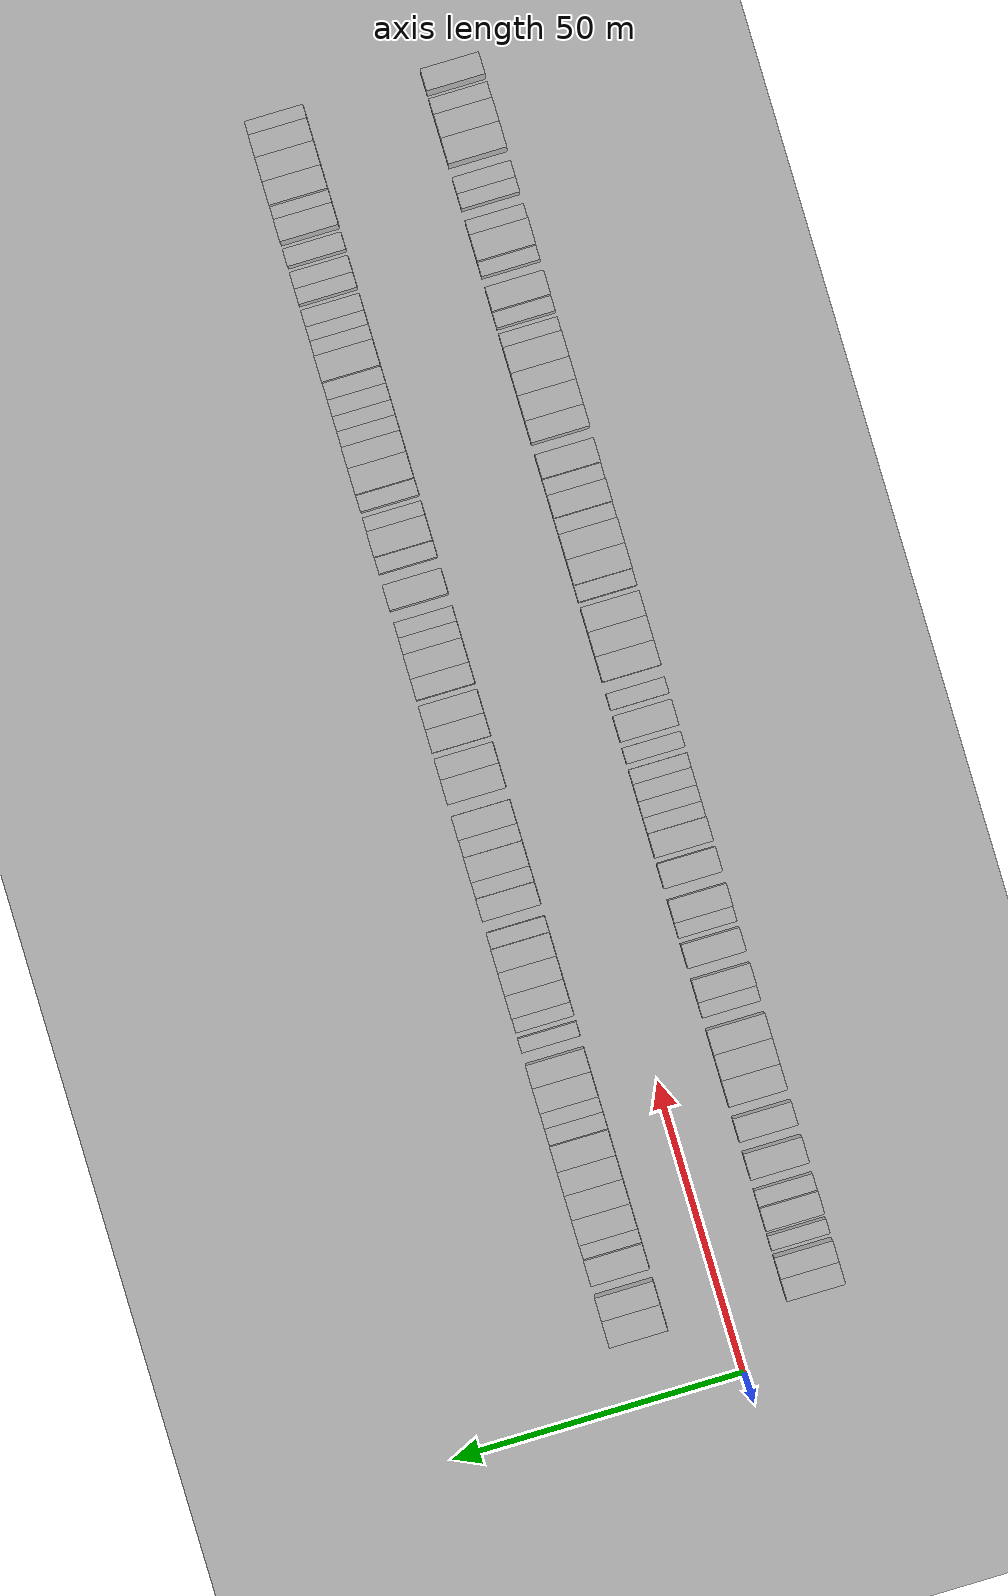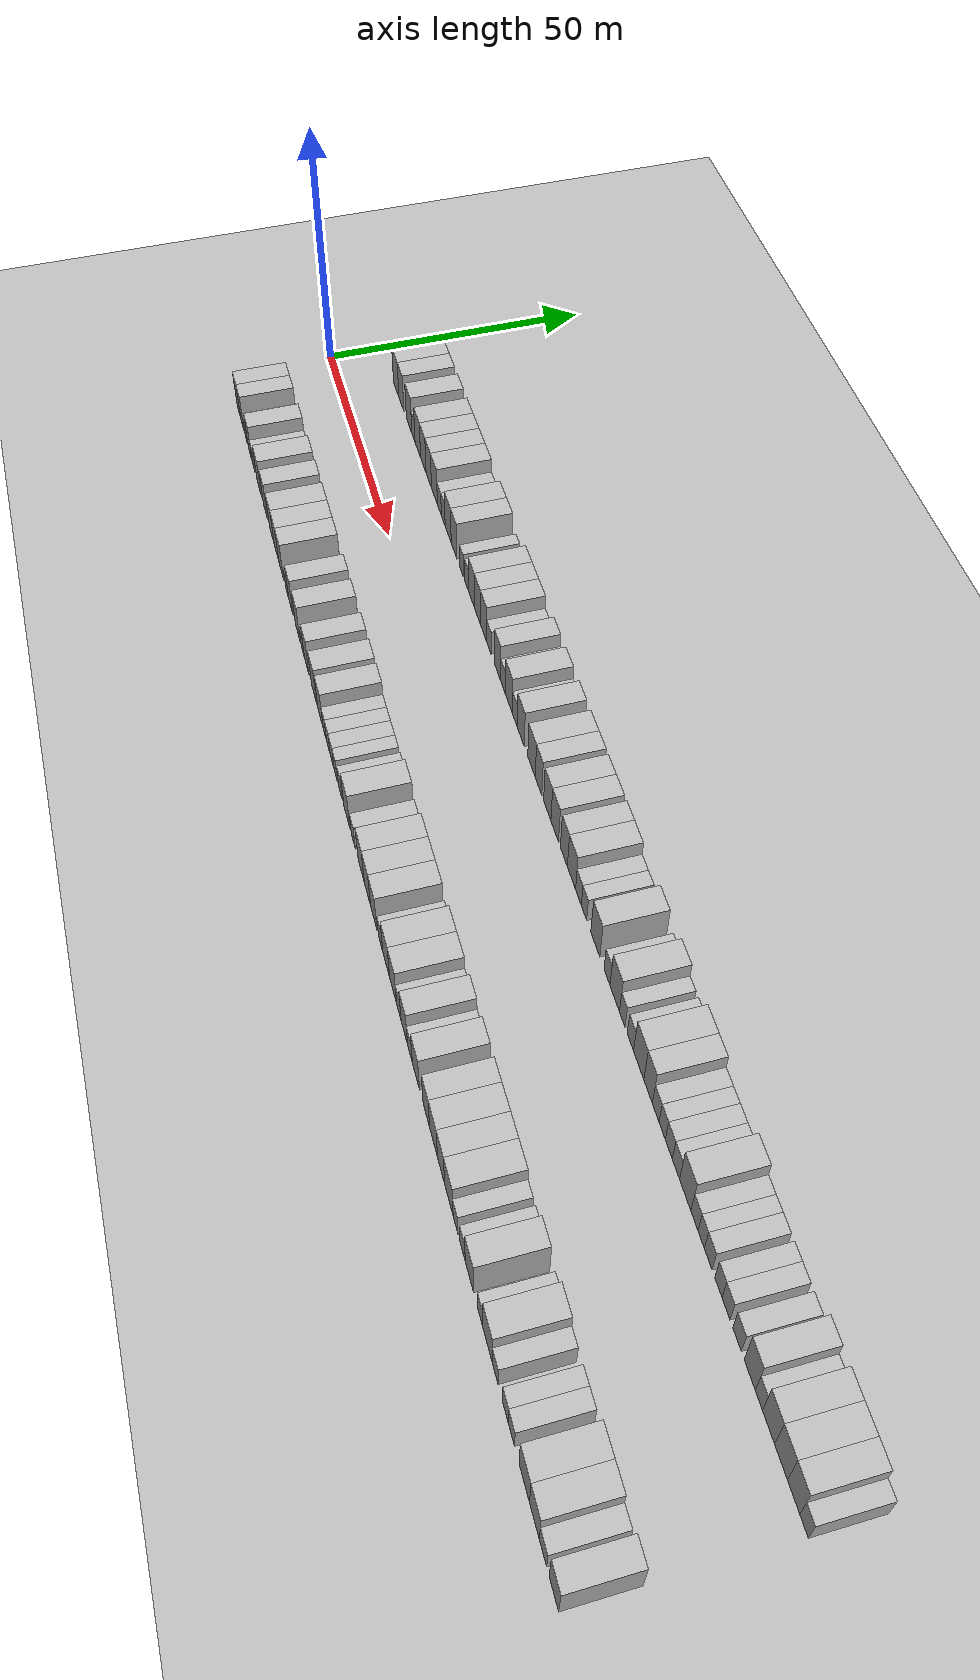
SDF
<?xml version="1.0" encoding="utf-8"?>

<sdf version="1.6">

   <world name="default">

      <gui fullscreen="0">

         <camera name="user_camera">

            <pose>-15 0 4.57585 0 0 0</pose>

            <view_controller>orbit</view_controller>

         </camera>

      </gui>

      <scene>

         <sky>

           <clouds>

             <speed>12</speed>

           </clouds>

         </sky>

         <ambient>0.4 0.4 0.4 1</ambient>

         <background>0.7 0.7 0.7 1</background>

         <shadows>1</shadows>

      </scene>

      <gravity>0 0 -9.8066</gravity>

      <magnetic_field>6e-06 2.3e-05 -4.2e-05</magnetic_field>

      <physics default="0" name="default_physics" type="ode">

         <ode>

            <solver>

               <type>quick</type>

               <iters>10</iters>

               <sor>1.0</sor>

               <use_dynamic_moi_rescaling>0</use_dynamic_moi_rescaling>

            </solver>

            <constraints>

               <cfm>0</cfm>

               <erp>0.2</erp>

               <contact_max_correcting_vel>100</contact_max_correcting_vel>

               <contact_surface_layer>0.001</contact_surface_layer>

            </constraints>

         </ode>

         <max_step_size>0.004</max_step_size>

         <real_time_factor>1</real_time_factor>

         <real_time_update_rate>250</real_time_update_rate>

      </physics>

      <light name="sun" type="directional">

         <cast_shadows>1</cast_shadows>

         <pose>0 0 10 0 0 0</pose>

         <diffuse>0.8 0.8 0.8 1</diffuse>

         <specular>0.2 0.2 0.2 1</specular>

         <attenuation>

            <range>1000</range>

            <constant>0.9</constant>

            <linear>0.01</linear>

            <quadratic>0.001</quadratic>

         </attenuation>

         <direction>-0.5 0.1 -0.9</direction>

      </light>

      <include>

         <name>ground_plane_1</name>

         <uri>model://HANNAS_ground_plane</uri>

         <pose>0 0 0  0 0 0</pose>

      </include>

      <include>

         <name>ground_plane_2</name>

         <uri>model://HANNAS_ground_plane</uri>

         <pose>100 0 0  0 0 0</pose>

      </include>

      <model name="building_1">

         <static>1</static>

         <pose frame="">13.2403 15.0000 0 0.000000 0.000000 1.570796</pose>

         <link name="link">

            <pose frame="">0 0 4.50 0 0 0</pose>

            <collision name="collision">

               <geometry>

                  <box>

                     <size>10.0000 4.4805 9.0000</size>

                  </box>

               </geometry>

               <max_contacts>10</max_contacts>

               <surface>

                  <contact>

                     <ode/>

                  </contact>

                  <bounce/>

                  <friction>

                     <torsional>

                        <ode/>

                     </torsional>

                     <ode/>

                  </friction>

               </surface>

            </collision>

            <visual name="visual">

               <cast_shadows>0</cast_shadows>

               <geometry>

                  <box>

                     <size>10.0000 4.4805 9.0000</size>

                  </box>

               </geometry>

               <material>

                  <script>

                     <uri>model://HANNAS_wall/materials/scripts</uri>

                     <uri>model://HANNAS_wall/materials/textures</uri>

                     <name>vrc/HANNAS_wall</name>

                  </script>

               </material>

            </visual>

            <self_collide>0</self_collide>

            <enable_wind>0</enable_wind>

            <kinematic>0</kinematic>

         </link>

      </model>

      <model name="building_2">

         <static>1</static>

         <pose frame="">17.4862 15.0000 0 0.000000 0.000000 1.570796</pose>

         <link name="link">

            <pose frame="">0 0 4.50 0 0 0</pose>

            <collision name="collision">

               <geometry>

                  <box>

                     <size>10.0000 4.0113 9.0000</size>

                  </box>

               </geometry>

               <max_contacts>10</max_contacts>

               <surface>

                  <contact>

                     <ode/>

                  </contact>

                  <bounce/>

                  <friction>

                     <torsional>

                        <ode/>

                     </torsional>

                     <ode/>

                  </friction>

               </surface>

            </collision>

            <visual name="visual">

               <cast_shadows>0</cast_shadows>

               <geometry>

                  <box>

                     <size>10.0000 4.0113 9.0000</size>

                  </box>

               </geometry>

               <material>

                  <script>

                     <uri>model://HANNAS_wall/materials/scripts</uri>

                     <uri>model://HANNAS_wall/materials/textures</uri>

                     <name>vrc/HANNAS_wall</name>

                  </script>

               </material>

            </visual>

            <self_collide>0</self_collide>

            <enable_wind>0</enable_wind>

            <kinematic>0</kinematic>

         </link>

      </model>

      <model name="building_3">

         <static>1</static>

         <pose frame="">23.6738 15.0000 0 0.000000 0.000000 1.570796</pose>

         <link name="link">

            <pose frame="">0 0 4.50 0 0 0</pose>

            <collision name="collision">

               <geometry>

                  <box>

                     <size>10.0000 4.3640 9.0000</size>

                  </box>

               </geometry>

               <max_contacts>10</max_contacts>

               <surface>

                  <contact>

                     <ode/>

                  </contact>

                  <bounce/>

                  <friction>

                     <torsional>

                        <ode/>

                     </torsional>

                     <ode/>

                  </friction>

               </surface>

            </collision>

            <visual name="visual">

               <cast_shadows>0</cast_shadows>

               <geometry>

                  <box>

                     <size>10.0000 4.3640 9.0000</size>

                  </box>

               </geometry>

               <material>

                  <script>

                     <uri>model://HANNAS_wall/materials/scripts</uri>

                     <uri>model://HANNAS_wall/materials/textures</uri>

                     <name>vrc/HANNAS_wall</name>

                  </script>

               </material>

            </visual>

            <self_collide>0</self_collide>

            <enable_wind>0</enable_wind>

            <kinematic>0</kinematic>

         </link>

      </model>

      <model name="building_4">

         <static>1</static>

         <pose frame="">27.1243 15.0000 0 0.000000 0.000000 1.570796</pose>

         <link name="link">

            <pose frame="">0 0 3.00 0 0 0</pose>

            <collision name="collision">

               <geometry>

                  <box>

                     <size>10.0000 2.5370 6.0000</size>

                  </box>

               </geometry>

               <max_contacts>10</max_contacts>

               <surface>

                  <contact>

                     <ode/>

                  </contact>

                  <bounce/>

                  <friction>

                     <torsional>

                        <ode/>

                     </torsional>

                     <ode/>

                  </friction>

               </surface>

            </collision>

            <visual name="visual">

               <cast_shadows>0</cast_shadows>

               <geometry>

                  <box>

                     <size>10.0000 2.5370 6.0000</size>

                  </box>

               </geometry>

               <material>

                  <script>

                     <uri>model://HANNAS_wall/materials/scripts</uri>

                     <uri>model://HANNAS_wall/materials/textures</uri>

                     <name>vrc/HANNAS_wall</name>

                  </script>

               </material>

            </visual>

            <self_collide>0</self_collide>

            <enable_wind>0</enable_wind>

            <kinematic>0</kinematic>

         </link>

      </model>

      <model name="building_5">

         <static>1</static>

         <pose frame="">30.5359 15.0000 0 0.000000 0.000000 1.570796</pose>

         <link name="link">

            <pose frame="">0 0 4.50 0 0 0</pose>

            <collision name="collision">

               <geometry>

                  <box>

                     <size>10.0000 4.2863 9.0000</size>

                  </box>

               </geometry>

               <max_contacts>10</max_contacts>

               <surface>

                  <contact>

                     <ode/>

                  </contact>

                  <bounce/>

                  <friction>

                     <torsional>

                        <ode/>

                     </torsional>

                     <ode/>

                  </friction>

               </surface>

            </collision>

            <visual name="visual">

               <cast_shadows>0</cast_shadows>

               <geometry>

                  <box>

                     <size>10.0000 4.2863 9.0000</size>

                  </box>

               </geometry>

               <material>

                  <script>

                     <uri>model://HANNAS_wall/materials/scripts</uri>

                     <uri>model://HANNAS_wall/materials/textures</uri>

                     <name>vrc/HANNAS_wall</name>

                  </script>

               </material>

            </visual>

            <self_collide>0</self_collide>

            <enable_wind>0</enable_wind>

            <kinematic>0</kinematic>

         </link>

      </model>

      <model name="building_6">

         <static>1</static>

         <pose frame="">34.7743 15.0000 0 0.000000 0.000000 1.570796</pose>

         <link name="link">

            <pose frame="">0 0 4.50 0 0 0</pose>

            <collision name="collision">

               <geometry>

                  <box>

                     <size>10.0000 4.1904 9.0000</size>

                  </box>

               </geometry>

               <max_contacts>10</max_contacts>

               <surface>

                  <contact>

                     <ode/>

                  </contact>

                  <bounce/>

                  <friction>

                     <torsional>

                        <ode/>

                     </torsional>

                     <ode/>

                  </friction>

               </surface>

            </collision>

            <visual name="visual">

               <cast_shadows>0</cast_shadows>

               <geometry>

                  <box>

                     <size>10.0000 4.1904 9.0000</size>

                  </box>

               </geometry>

               <material>

                  <script>

                     <uri>model://HANNAS_wall/materials/scripts</uri>

                     <uri>model://HANNAS_wall/materials/textures</uri>

                     <name>vrc/HANNAS_wall</name>

                  </script>

               </material>

            </visual>

            <self_collide>0</self_collide>

            <enable_wind>0</enable_wind>

            <kinematic>0</kinematic>

         </link>

      </model>

      <model name="building_7">

         <static>1</static>

         <pose frame="">38.8950 15.0000 0 0.000000 0.000000 1.570796</pose>

         <link name="link">

            <pose frame="">0 0 4.50 0 0 0</pose>

            <collision name="collision">

               <geometry>

                  <box>

                     <size>10.0000 4.0511 9.0000</size>

                  </box>

               </geometry>

               <max_contacts>10</max_contacts>

               <surface>

                  <contact>

                     <ode/>

                  </contact>

                  <bounce/>

                  <friction>

                     <torsional>

                        <ode/>

                     </torsional>

                     <ode/>

                  </friction>

               </surface>

            </collision>

            <visual name="visual">

               <cast_shadows>0</cast_shadows>

               <geometry>

                  <box>

                     <size>10.0000 4.0511 9.0000</size>

                  </box>

               </geometry>

               <material>

                  <script>

                     <uri>model://HANNAS_wall/materials/scripts</uri>

                     <uri>model://HANNAS_wall/materials/textures</uri>

                     <name>vrc/HANNAS_wall</name>

                  </script>

               </material>

            </visual>

            <self_collide>0</self_collide>

            <enable_wind>0</enable_wind>

            <kinematic>0</kinematic>

         </link>

      </model>

      <model name="building_8">

         <static>1</static>

         <pose frame="">43.1086 15.0000 0 0.000000 0.000000 1.570796</pose>

         <link name="link">

            <pose frame="">0 0 4.50 0 0 0</pose>

            <collision name="collision">

               <geometry>

                  <box>

                     <size>10.0000 4.3761 9.0000</size>

                  </box>

               </geometry>

               <max_contacts>10</max_contacts>

               <surface>

                  <contact>

                     <ode/>

                  </contact>

                  <bounce/>

                  <friction>

                     <torsional>

                        <ode/>

                     </torsional>

                     <ode/>

                  </friction>

               </surface>

            </collision>

            <visual name="visual">

               <cast_shadows>0</cast_shadows>

               <geometry>

                  <box>

                     <size>10.0000 4.3761 9.0000</size>

                  </box>

               </geometry>

               <material>

                  <script>

                     <uri>model://HANNAS_wall/materials/scripts</uri>

                     <uri>model://HANNAS_wall/materials/textures</uri>

                     <name>vrc/HANNAS_wall</name>

                  </script>

               </material>

            </visual>

            <self_collide>0</self_collide>

            <enable_wind>0</enable_wind>

            <kinematic>0</kinematic>

         </link>

      </model>

      <model name="building_9">

         <static>1</static>

         <pose frame="">46.7246 15.0000 0 0.000000 0.000000 1.570796</pose>

         <link name="link">

            <pose frame="">0 0 3.00 0 0 0</pose>

            <collision name="collision">

               <geometry>

                  <box>

                     <size>10.0000 2.8559 6.0000</size>

                  </box>

               </geometry>

               <max_contacts>10</max_contacts>

               <surface>

                  <contact>

                     <ode/>

                  </contact>

                  <bounce/>

                  <friction>

                     <torsional>

                        <ode/>

                     </torsional>

                     <ode/>

                  </friction>

               </surface>

            </collision>

            <visual name="visual">

               <cast_shadows>0</cast_shadows>

               <geometry>

                  <box>

                     <size>10.0000 2.8559 6.0000</size>

                  </box>

               </geometry>

               <material>

                  <script>

                     <uri>model://HANNAS_wall/materials/scripts</uri>

                     <uri>model://HANNAS_wall/materials/textures</uri>

                     <name>vrc/HANNAS_wall</name>

                  </script>

               </material>

            </visual>

            <self_collide>0</self_collide>

            <enable_wind>0</enable_wind>

            <kinematic>0</kinematic>

         </link>

      </model>

      <model name="building_10">

         <static>1</static>

         <pose frame="">49.5225 15.0000 0 0.000000 0.000000 1.570796</pose>

         <link name="link">

            <pose frame="">0 0 3.00 0 0 0</pose>

            <collision name="collision">

               <geometry>

                  <box>

                     <size>10.0000 2.7400 6.0000</size>

                  </box>

               </geometry>

               <max_contacts>10</max_contacts>

               <surface>

                  <contact>

                     <ode/>

                  </contact>

                  <bounce/>

                  <friction>

                     <torsional>

                        <ode/>

                     </torsional>

                     <ode/>

                  </friction>

               </surface>

            </collision>

            <visual name="visual">

               <cast_shadows>0</cast_shadows>

               <geometry>

                  <box>

                     <size>10.0000 2.7400 6.0000</size>

                  </box>

               </geometry>

               <material>

                  <script>

                     <uri>model://HANNAS_wall/materials/scripts</uri>

                     <uri>model://HANNAS_wall/materials/textures</uri>

                     <name>vrc/HANNAS_wall</name>

                  </script>

               </material>

            </visual>

            <self_collide>0</self_collide>

            <enable_wind>0</enable_wind>

            <kinematic>0</kinematic>

         </link>

      </model>

      <model name="building_11">

         <static>1</static>

         <pose frame="">53.0292 15.0000 0 0.000000 0.000000 1.570796</pose>

         <link name="link">

            <pose frame="">0 0 4.50 0 0 0</pose>

            <collision name="collision">

               <geometry>

                  <box>

                     <size>10.0000 4.2733 9.0000</size>

                  </box>

               </geometry>

               <max_contacts>10</max_contacts>

               <surface>

                  <contact>

                     <ode/>

                  </contact>

                  <bounce/>

                  <friction>

                     <torsional>

                        <ode/>

                     </torsional>

                     <ode/>

                  </friction>

               </surface>

            </collision>

            <visual name="visual">

               <cast_shadows>0</cast_shadows>

               <geometry>

                  <box>

                     <size>10.0000 4.2733 9.0000</size>

                  </box>

               </geometry>

               <material>

                  <script>

                     <uri>model://HANNAS_wall/materials/scripts</uri>

                     <uri>model://HANNAS_wall/materials/textures</uri>

                     <name>vrc/HANNAS_wall</name>

                  </script>

               </material>

            </visual>

            <self_collide>0</self_collide>

            <enable_wind>0</enable_wind>

            <kinematic>0</kinematic>

         </link>

      </model>

      <model name="building_12">

         <static>1</static>

         <pose frame="">57.1540 15.0000 0 0.000000 0.000000 1.570796</pose>

         <link name="link">

            <pose frame="">0 0 4.50 0 0 0</pose>

            <collision name="collision">

               <geometry>

                  <box>

                     <size>10.0000 3.9763 9.0000</size>

                  </box>

               </geometry>

               <max_contacts>10</max_contacts>

               <surface>

                  <contact>

                     <ode/>

                  </contact>

                  <bounce/>

                  <friction>

                     <torsional>

                        <ode/>

                     </torsional>

                     <ode/>

                  </friction>

               </surface>

            </collision>

            <visual name="visual">

               <cast_shadows>0</cast_shadows>

               <geometry>

                  <box>

                     <size>10.0000 3.9763 9.0000</size>

                  </box>

               </geometry>

               <material>

                  <script>

                     <uri>model://HANNAS_wall/materials/scripts</uri>

                     <uri>model://HANNAS_wall/materials/textures</uri>

                     <name>vrc/HANNAS_wall</name>

                  </script>

               </material>

            </visual>

            <self_collide>0</self_collide>

            <enable_wind>0</enable_wind>

            <kinematic>0</kinematic>

         </link>

      </model>

      <model name="building_13">

         <static>1</static>

         <pose frame="">62.3634 15.0000 0 0.000000 0.000000 1.570796</pose>

         <link name="link">

            <pose frame="">0 0 3.00 0 0 0</pose>

            <collision name="collision">

               <geometry>

                  <box>

                     <size>10.0000 2.4425 6.0000</size>

                  </box>

               </geometry>

               <max_contacts>10</max_contacts>

               <surface>

                  <contact>

                     <ode/>

                  </contact>

                  <bounce/>

                  <friction>

                     <torsional>

                        <ode/>

                     </torsional>

                     <ode/>

                  </friction>

               </surface>

            </collision>

            <visual name="visual">

               <cast_shadows>0</cast_shadows>

               <geometry>

                  <box>

                     <size>10.0000 2.4425 6.0000</size>

                  </box>

               </geometry>

               <material>

                  <script>

                     <uri>model://HANNAS_wall/materials/scripts</uri>

                     <uri>model://HANNAS_wall/materials/textures</uri>

                     <name>vrc/HANNAS_wall</name>

                  </script>

               </material>

            </visual>

            <self_collide>0</self_collide>

            <enable_wind>0</enable_wind>

            <kinematic>0</kinematic>

         </link>

      </model>

      <model name="building_14">

         <static>1</static>

         <pose frame="">65.8140 15.0000 0 0.000000 0.000000 1.570796</pose>

         <link name="link">

            <pose frame="">0 0 3.00 0 0 0</pose>

            <collision name="collision">

               <geometry>

                  <box>

                     <size>10.0000 2.4586 6.0000</size>

                  </box>

               </geometry>

               <max_contacts>10</max_contacts>

               <surface>

                  <contact>

                     <ode/>

                  </contact>

                  <bounce/>

                  <friction>

                     <torsional>

                        <ode/>

                     </torsional>

                     <ode/>

                  </friction>

               </surface>

            </collision>

            <visual name="visual">

               <cast_shadows>0</cast_shadows>

               <geometry>

                  <box>

                     <size>10.0000 2.4586 6.0000</size>

                  </box>

               </geometry>

               <material>

                  <script>

                     <uri>model://HANNAS_wall/materials/scripts</uri>

                     <uri>model://HANNAS_wall/materials/textures</uri>

                     <name>vrc/HANNAS_wall</name>

                  </script>

               </material>

            </visual>

            <self_collide>0</self_collide>

            <enable_wind>0</enable_wind>

            <kinematic>0</kinematic>

         </link>

      </model>

      <model name="building_15">

         <static>1</static>

         <pose frame="">68.9917 15.0000 0 0.000000 0.000000 1.570796</pose>

         <link name="link">

            <pose frame="">0 0 4.50 0 0 0</pose>

            <collision name="collision">

               <geometry>

                  <box>

                     <size>10.0000 3.8968 9.0000</size>

                  </box>

               </geometry>

               <max_contacts>10</max_contacts>

               <surface>

                  <contact>

                     <ode/>

                  </contact>

                  <bounce/>

                  <friction>

                     <torsional>

                        <ode/>

                     </torsional>

                     <ode/>

                  </friction>

               </surface>

            </collision>

            <visual name="visual">

               <cast_shadows>0</cast_shadows>

               <geometry>

                  <box>

                     <size>10.0000 3.8968 9.0000</size>

                  </box>

               </geometry>

               <material>

                  <script>

                     <uri>model://HANNAS_wall/materials/scripts</uri>

                     <uri>model://HANNAS_wall/materials/textures</uri>

                     <name>vrc/HANNAS_wall</name>

                  </script>

               </material>

            </visual>

            <self_collide>0</self_collide>

            <enable_wind>0</enable_wind>

            <kinematic>0</kinematic>

         </link>

      </model>

      <model name="building_16">

         <static>1</static>

         <pose frame="">72.9153 15.0000 0 0.000000 0.000000 1.570796</pose>

         <link name="link">

            <pose frame="">0 0 4.50 0 0 0</pose>

            <collision name="collision">

               <geometry>

                  <box>

                     <size>10.0000 3.9504 9.0000</size>

                  </box>

               </geometry>

               <max_contacts>10</max_contacts>

               <surface>

                  <contact>

                     <ode/>

                  </contact>

                  <bounce/>

                  <friction>

                     <torsional>

                        <ode/>

                     </torsional>

                     <ode/>

                  </friction>

               </surface>

            </collision>

            <visual name="visual">

               <cast_shadows>0</cast_shadows>

               <geometry>

                  <box>

                     <size>10.0000 3.9504 9.0000</size>

                  </box>

               </geometry>

               <material>

                  <script>

                     <uri>model://HANNAS_wall/materials/scripts</uri>

                     <uri>model://HANNAS_wall/materials/textures</uri>

                     <name>vrc/HANNAS_wall</name>

                  </script>

               </material>

            </visual>

            <self_collide>0</self_collide>

            <enable_wind>0</enable_wind>

            <kinematic>0</kinematic>

         </link>

      </model>

      <model name="building_17">

         <static>1</static>

         <pose frame="">76.8977 15.0000 0 0.000000 0.000000 1.570796</pose>

         <link name="link">

            <pose frame="">0 0 4.50 0 0 0</pose>

            <collision name="collision">

               <geometry>

                  <box>

                     <size>10.0000 4.0143 9.0000</size>

                  </box>

               </geometry>

               <max_contacts>10</max_contacts>

               <surface>

                  <contact>

                     <ode/>

                  </contact>

                  <bounce/>

                  <friction>

                     <torsional>

                        <ode/>

                     </torsional>

                     <ode/>

                  </friction>

               </surface>

            </collision>

            <visual name="visual">

               <cast_shadows>0</cast_shadows>

               <geometry>

                  <box>

                     <size>10.0000 4.0143 9.0000</size>

                  </box>

               </geometry>

               <material>

                  <script>

                     <uri>model://HANNAS_wall/materials/scripts</uri>

                     <uri>model://HANNAS_wall/materials/textures</uri>

                     <name>vrc/HANNAS_wall</name>

                  </script>

               </material>

            </visual>

            <self_collide>0</self_collide>

            <enable_wind>0</enable_wind>

            <kinematic>0</kinematic>

         </link>

      </model>

      <model name="building_18">

         <static>1</static>

         <pose frame="">80.2734 15.0000 0 0.000000 0.000000 1.570796</pose>

         <link name="link">

            <pose frame="">0 0 3.00 0 0 0</pose>

            <collision name="collision">

               <geometry>

                  <box>

                     <size>10.0000 2.7371 6.0000</size>

                  </box>

               </geometry>

               <max_contacts>10</max_contacts>

               <surface>

                  <contact>

                     <ode/>

                  </contact>

                  <bounce/>

                  <friction>

                     <torsional>

                        <ode/>

                     </torsional>

                     <ode/>

                  </friction>

               </surface>

            </collision>

            <visual name="visual">

               <cast_shadows>0</cast_shadows>

               <geometry>

                  <box>

                     <size>10.0000 2.7371 6.0000</size>

                  </box>

               </geometry>

               <material>

                  <script>

                     <uri>model://HANNAS_wall/materials/scripts</uri>

                     <uri>model://HANNAS_wall/materials/textures</uri>

                     <name>vrc/HANNAS_wall</name>

                  </script>

               </material>

            </visual>

            <self_collide>0</self_collide>

            <enable_wind>0</enable_wind>

            <kinematic>0</kinematic>

         </link>

      </model>

      <model name="building_19">

         <static>1</static>

         <pose frame="">85.5805 15.0000 0 0.000000 0.000000 1.570796</pose>

         <link name="link">

            <pose frame="">0 0 4.50 0 0 0</pose>

            <collision name="collision">

               <geometry>

                  <box>

                     <size>10.0000 3.8772 9.0000</size>

                  </box>

               </geometry>

               <max_contacts>10</max_contacts>

               <surface>

                  <contact>

                     <ode/>

                  </contact>

                  <bounce/>

                  <friction>

                     <torsional>

                        <ode/>

                     </torsional>

                     <ode/>

                  </friction>

               </surface>

            </collision>

            <visual name="visual">

               <cast_shadows>0</cast_shadows>

               <geometry>

                  <box>

                     <size>10.0000 3.8772 9.0000</size>

                  </box>

               </geometry>

               <material>

                  <script>

                     <uri>model://HANNAS_wall/materials/scripts</uri>

                     <uri>model://HANNAS_wall/materials/textures</uri>

                     <name>vrc/HANNAS_wall</name>

                  </script>

               </material>

            </visual>

            <self_collide>0</self_collide>

            <enable_wind>0</enable_wind>

            <kinematic>0</kinematic>

         </link>

      </model>

      <model name="building_20">

         <static>1</static>

         <pose frame="">88.8902 15.0000 0 0.000000 0.000000 1.570796</pose>

         <link name="link">

            <pose frame="">0 0 3.00 0 0 0</pose>

            <collision name="collision">

               <geometry>

                  <box>

                     <size>10.0000 2.7421 6.0000</size>

                  </box>

               </geometry>

               <max_contacts>10</max_contacts>

               <surface>

                  <contact>

                     <ode/>

                  </contact>

                  <bounce/>

                  <friction>

                     <torsional>

                        <ode/>

                     </torsional>

                     <ode/>

                  </friction>

               </surface>

            </collision>

            <visual name="visual">

               <cast_shadows>0</cast_shadows>

               <geometry>

                  <box>

                     <size>10.0000 2.7421 6.0000</size>

                  </box>

               </geometry>

               <material>

                  <script>

                     <uri>model://HANNAS_wall/materials/scripts</uri>

                     <uri>model://HANNAS_wall/materials/textures</uri>

                     <name>vrc/HANNAS_wall</name>

                  </script>

               </material>

            </visual>

            <self_collide>0</self_collide>

            <enable_wind>0</enable_wind>

            <kinematic>0</kinematic>

         </link>

      </model>

      <model name="building_21">

         <static>1</static>

         <pose frame="">92.3960 15.0000 0 0.000000 0.000000 1.570796</pose>

         <link name="link">

            <pose frame="">0 0 4.50 0 0 0</pose>

            <collision name="collision">

               <geometry>

                  <box>

                     <size>10.0000 4.2694 9.0000</size>

                  </box>

               </geometry>

               <max_contacts>10</max_contacts>

               <surface>

                  <contact>

                     <ode/>

                  </contact>

                  <bounce/>

                  <friction>

                     <torsional>

                        <ode/>

                     </torsional>

                     <ode/>

                  </friction>

               </surface>

            </collision>

            <visual name="visual">

               <cast_shadows>0</cast_shadows>

               <geometry>

                  <box>

                     <size>10.0000 4.2694 9.0000</size>

                  </box>

               </geometry>

               <material>

                  <script>

                     <uri>model://HANNAS_wall/materials/scripts</uri>

                     <uri>model://HANNAS_wall/materials/textures</uri>

                     <name>vrc/HANNAS_wall</name>

                  </script>

               </material>

            </visual>

            <self_collide>0</self_collide>

            <enable_wind>0</enable_wind>

            <kinematic>0</kinematic>

         </link>

      </model>

      <model name="building_22">

         <static>1</static>

         <pose frame="">96.0144 15.0000 0 0.000000 0.000000 1.570796</pose>

         <link name="link">

            <pose frame="">0 0 3.00 0 0 0</pose>

            <collision name="collision">

               <geometry>

                  <box>

                     <size>10.0000 2.9675 6.0000</size>

                  </box>

               </geometry>

               <max_contacts>10</max_contacts>

               <surface>

                  <contact>

                     <ode/>

                  </contact>

                  <bounce/>

                  <friction>

                     <torsional>

                        <ode/>

                     </torsional>

                     <ode/>

                  </friction>

               </surface>

            </collision>

            <visual name="visual">

               <cast_shadows>0</cast_shadows>

               <geometry>

                  <box>

                     <size>10.0000 2.9675 6.0000</size>

                  </box>

               </geometry>

               <material>

                  <script>

                     <uri>model://HANNAS_wall/materials/scripts</uri>

                     <uri>model://HANNAS_wall/materials/textures</uri>

                     <name>vrc/HANNAS_wall</name>

                  </script>

               </material>

            </visual>

            <self_collide>0</self_collide>

            <enable_wind>0</enable_wind>

            <kinematic>0</kinematic>

         </link>

      </model>

      <model name="building_23">

         <static>1</static>

         <pose frame="">99.5372 15.0000 0 0.000000 0.000000 1.570796</pose>

         <link name="link">

            <pose frame="">0 0 4.50 0 0 0</pose>

            <collision name="collision">

               <geometry>

                  <box>

                     <size>10.0000 4.0781 9.0000</size>

                  </box>

               </geometry>

               <max_contacts>10</max_contacts>

               <surface>

                  <contact>

                     <ode/>

                  </contact>

                  <bounce/>

                  <friction>

                     <torsional>

                        <ode/>

                     </torsional>

                     <ode/>

                  </friction>

               </surface>

            </collision>

            <visual name="visual">

               <cast_shadows>0</cast_shadows>

               <geometry>

                  <box>

                     <size>10.0000 4.0781 9.0000</size>

                  </box>

               </geometry>

               <material>

                  <script>

                     <uri>model://HANNAS_wall/materials/scripts</uri>

                     <uri>model://HANNAS_wall/materials/textures</uri>

                     <name>vrc/HANNAS_wall</name>

                  </script>

               </material>

            </visual>

            <self_collide>0</self_collide>

            <enable_wind>0</enable_wind>

            <kinematic>0</kinematic>

         </link>

      </model>

      <model name="building_24">

         <static>1</static>

         <pose frame="">105.6839 15.0000 0 0.000000 0.000000 1.570796</pose>

         <link name="link">

            <pose frame="">0 0 4.50 0 0 0</pose>

            <collision name="collision">

               <geometry>

                  <box>

                     <size>10.0000 4.2154 9.0000</size>

                  </box>

               </geometry>

               <max_contacts>10</max_contacts>

               <surface>

                  <contact>

                     <ode/>

                  </contact>

                  <bounce/>

                  <friction>

                     <torsional>

                        <ode/>

                     </torsional>

                     <ode/>

                  </friction>

               </surface>

            </collision>

            <visual name="visual">

               <cast_shadows>0</cast_shadows>

               <geometry>

                  <box>

                     <size>10.0000 4.2154 9.0000</size>

                  </box>

               </geometry>

               <material>

                  <script>

                     <uri>model://HANNAS_wall/materials/scripts</uri>

                     <uri>model://HANNAS_wall/materials/textures</uri>

                     <name>vrc/HANNAS_wall</name>

                  </script>

               </material>

            </visual>

            <self_collide>0</self_collide>

            <enable_wind>0</enable_wind>

            <kinematic>0</kinematic>

         </link>

      </model>

      <model name="building_25">

         <static>1</static>

         <pose frame="">109.6026 15.0000 0 0.000000 0.000000 1.570796</pose>

         <link name="link">

            <pose frame="">0 0 4.50 0 0 0</pose>

            <collision name="collision">

               <geometry>

                  <box>

                     <size>10.0000 3.6221 9.0000</size>

                  </box>

               </geometry>

               <max_contacts>10</max_contacts>

               <surface>

                  <contact>

                     <ode/>

                  </contact>

                  <bounce/>

                  <friction>

                     <torsional>

                        <ode/>

                     </torsional>

                     <ode/>

                  </friction>

               </surface>

            </collision>

            <visual name="visual">

               <cast_shadows>0</cast_shadows>

               <geometry>

                  <box>

                     <size>10.0000 3.6221 9.0000</size>

                  </box>

               </geometry>

               <material>

                  <script>

                     <uri>model://HANNAS_wall/materials/scripts</uri>

                     <uri>model://HANNAS_wall/materials/textures</uri>

                     <name>vrc/HANNAS_wall</name>

                  </script>

               </material>

            </visual>

            <self_collide>0</self_collide>

            <enable_wind>0</enable_wind>

            <kinematic>0</kinematic>

         </link>

      </model>

      <model name="building_26">

         <static>1</static>

         <pose frame="">114.3878 15.0000 0 0.000000 0.000000 1.570796</pose>

         <link name="link">

            <pose frame="">0 0 4.50 0 0 0</pose>

            <collision name="collision">

               <geometry>

                  <box>

                     <size>10.0000 3.9483 9.0000</size>

                  </box>

               </geometry>

               <max_contacts>10</max_contacts>

               <surface>

                  <contact>

                     <ode/>

                  </contact>

                  <bounce/>

                  <friction>

                     <torsional>

                        <ode/>

                     </torsional>

                     <ode/>

                  </friction>

               </surface>

            </collision>

            <visual name="visual">

               <cast_shadows>0</cast_shadows>

               <geometry>

                  <box>

                     <size>10.0000 3.9483 9.0000</size>

                  </box>

               </geometry>

               <material>

                  <script>

                     <uri>model://HANNAS_wall/materials/scripts</uri>

                     <uri>model://HANNAS_wall/materials/textures</uri>

                     <name>vrc/HANNAS_wall</name>

                  </script>

               </material>

            </visual>

            <self_collide>0</self_collide>

            <enable_wind>0</enable_wind>

            <kinematic>0</kinematic>

         </link>

      </model>

      <model name="building_27">

         <static>1</static>

         <pose frame="">118.3760 15.0000 0 0.000000 0.000000 1.570796</pose>

         <link name="link">

            <pose frame="">0 0 4.50 0 0 0</pose>

            <collision name="collision">

               <geometry>

                  <box>

                     <size>10.0000 4.0280 9.0000</size>

                  </box>

               </geometry>

               <max_contacts>10</max_contacts>

               <surface>

                  <contact>

                     <ode/>

                  </contact>

                  <bounce/>

                  <friction>

                     <torsional>

                        <ode/>

                     </torsional>

                     <ode/>

                  </friction>

               </surface>

            </collision>

            <visual name="visual">

               <cast_shadows>0</cast_shadows>

               <geometry>

                  <box>

                     <size>10.0000 4.0280 9.0000</size>

                  </box>

               </geometry>

               <material>

                  <script>

                     <uri>model://HANNAS_wall/materials/scripts</uri>

                     <uri>model://HANNAS_wall/materials/textures</uri>

                     <name>vrc/HANNAS_wall</name>

                  </script>

               </material>

            </visual>

            <self_collide>0</self_collide>

            <enable_wind>0</enable_wind>

            <kinematic>0</kinematic>

         </link>

      </model>

      <model name="building_28">

         <static>1</static>

         <pose frame="">123.1927 15.0000 0 0.000000 0.000000 1.570796</pose>

         <link name="link">

            <pose frame="">0 0 4.50 0 0 0</pose>

            <collision name="collision">

               <geometry>

                  <box>

                     <size>10.0000 3.6054 9.0000</size>

                  </box>

               </geometry>

               <max_contacts>10</max_contacts>

               <surface>

                  <contact>

                     <ode/>

                  </contact>

                  <bounce/>

                  <friction>

                     <torsional>

                        <ode/>

                     </torsional>

                     <ode/>

                  </friction>

               </surface>

            </collision>

            <visual name="visual">

               <cast_shadows>0</cast_shadows>

               <geometry>

                  <box>

                     <size>10.0000 3.6054 9.0000</size>

                  </box>

               </geometry>

               <material>

                  <script>

                     <uri>model://HANNAS_wall/materials/scripts</uri>

                     <uri>model://HANNAS_wall/materials/textures</uri>

                     <name>vrc/HANNAS_wall</name>

                  </script>

               </material>

            </visual>

            <self_collide>0</self_collide>

            <enable_wind>0</enable_wind>

            <kinematic>0</kinematic>

         </link>

      </model>

      <model name="building_29">

         <static>1</static>

         <pose frame="">127.0830 15.0000 0 0.000000 0.000000 1.570796</pose>

         <link name="link">

            <pose frame="">0 0 4.50 0 0 0</pose>

            <collision name="collision">

               <geometry>

                  <box>

                     <size>10.0000 4.1753 9.0000</size>

                  </box>

               </geometry>

               <max_contacts>10</max_contacts>

               <surface>

                  <contact>

                     <ode/>

                  </contact>

                  <bounce/>

                  <friction>

                     <torsional>

                        <ode/>

                     </torsional>

                     <ode/>

                  </friction>

               </surface>

            </collision>

            <visual name="visual">

               <cast_shadows>0</cast_shadows>

               <geometry>

                  <box>

                     <size>10.0000 4.1753 9.0000</size>

                  </box>

               </geometry>

               <material>

                  <script>

                     <uri>model://HANNAS_wall/materials/scripts</uri>

                     <uri>model://HANNAS_wall/materials/textures</uri>

                     <name>vrc/HANNAS_wall</name>

                  </script>

               </material>

            </visual>

            <self_collide>0</self_collide>

            <enable_wind>0</enable_wind>

            <kinematic>0</kinematic>

         </link>

      </model>

      <model name="building_30">

         <static>1</static>

         <pose frame="">130.6172 15.0000 0 0.000000 0.000000 1.570796</pose>

         <link name="link">

            <pose frame="">0 0 3.00 0 0 0</pose>

            <collision name="collision">

               <geometry>

                  <box>

                     <size>10.0000 2.8932 6.0000</size>

                  </box>

               </geometry>

               <max_contacts>10</max_contacts>

               <surface>

                  <contact>

                     <ode/>

                  </contact>

                  <bounce/>

                  <friction>

                     <torsional>

                        <ode/>

                     </torsional>

                     <ode/>

                  </friction>

               </surface>

            </collision>

            <visual name="visual">

               <cast_shadows>0</cast_shadows>

               <geometry>

                  <box>

                     <size>10.0000 2.8932 6.0000</size>

                  </box>

               </geometry>

               <material>

                  <script>

                     <uri>model://HANNAS_wall/materials/scripts</uri>

                     <uri>model://HANNAS_wall/materials/textures</uri>

                     <name>vrc/HANNAS_wall</name>

                  </script>

               </material>

            </visual>

            <self_collide>0</self_collide>

            <enable_wind>0</enable_wind>

            <kinematic>0</kinematic>

         </link>

      </model>

      <model name="building_31">

         <static>1</static>

         <pose frame="">133.3781 15.0000 0 0.000000 0.000000 1.570796</pose>

         <link name="link">

            <pose frame="">0 0 3.00 0 0 0</pose>

            <collision name="collision">

               <geometry>

                  <box>

                     <size>10.0000 2.6285 6.0000</size>

                  </box>

               </geometry>

               <max_contacts>10</max_contacts>

               <surface>

                  <contact>

                     <ode/>

                  </contact>

                  <bounce/>

                  <friction>

                     <torsional>

                        <ode/>

                     </torsional>

                     <ode/>

                  </friction>

               </surface>

            </collision>

            <visual name="visual">

               <cast_shadows>0</cast_shadows>

               <geometry>

                  <box>

                     <size>10.0000 2.6285 6.0000</size>

                  </box>

               </geometry>

               <material>

                  <script>

                     <uri>model://HANNAS_wall/materials/scripts</uri>

                     <uri>model://HANNAS_wall/materials/textures</uri>

                     <name>vrc/HANNAS_wall</name>

                  </script>

               </material>

            </visual>

            <self_collide>0</self_collide>

            <enable_wind>0</enable_wind>

            <kinematic>0</kinematic>

         </link>

      </model>

      <model name="building_32">

         <static>1</static>

         <pose frame="">138.8617 15.0000 0 0.000000 0.000000 1.570796</pose>

         <link name="link">

            <pose frame="">0 0 4.50 0 0 0</pose>

            <collision name="collision">

               <geometry>

                  <box>

                     <size>10.0000 4.3386 9.0000</size>

                  </box>

               </geometry>

               <max_contacts>10</max_contacts>

               <surface>

                  <contact>

                     <ode/>

                  </contact>

                  <bounce/>

                  <friction>

                     <torsional>

                        <ode/>

                     </torsional>

                     <ode/>

                  </friction>

               </surface>

            </collision>

            <visual name="visual">

               <cast_shadows>0</cast_shadows>

               <geometry>

                  <box>

                     <size>10.0000 4.3386 9.0000</size>

                  </box>

               </geometry>

               <material>

                  <script>

                     <uri>model://HANNAS_wall/materials/scripts</uri>

                     <uri>model://HANNAS_wall/materials/textures</uri>

                     <name>vrc/HANNAS_wall</name>

                  </script>

               </material>

            </visual>

            <self_collide>0</self_collide>

            <enable_wind>0</enable_wind>

            <kinematic>0</kinematic>

         </link>

      </model>

      <model name="building_33">

         <static>1</static>

         <pose frame="">144.4029 15.0000 0 0.000000 0.000000 1.570796</pose>

         <link name="link">

            <pose frame="">0 0 3.00 0 0 0</pose>

            <collision name="collision">

               <geometry>

                  <box>

                     <size>10.0000 2.7437 6.0000</size>

                  </box>

               </geometry>

               <max_contacts>10</max_contacts>

               <surface>

                  <contact>

                     <ode/>

                  </contact>

                  <bounce/>

                  <friction>

                     <torsional>

                        <ode/>

                     </torsional>

                     <ode/>

                  </friction>

               </surface>

            </collision>

            <visual name="visual">

               <cast_shadows>0</cast_shadows>

               <geometry>

                  <box>

                     <size>10.0000 2.7437 6.0000</size>

                  </box>

               </geometry>

               <material>

                  <script>

                     <uri>model://HANNAS_wall/materials/scripts</uri>

                     <uri>model://HANNAS_wall/materials/textures</uri>

                     <name>vrc/HANNAS_wall</name>

                  </script>

               </material>

            </visual>

            <self_collide>0</self_collide>

            <enable_wind>0</enable_wind>

            <kinematic>0</kinematic>

         </link>

      </model>

      <model name="building_34">

         <static>1</static>

         <pose frame="">147.9562 15.0000 0 0.000000 0.000000 1.570796</pose>

         <link name="link">

            <pose frame="">0 0 4.50 0 0 0</pose>

            <collision name="collision">

               <geometry>

                  <box>

                     <size>10.0000 4.3629 9.0000</size>

                  </box>

               </geometry>

               <max_contacts>10</max_contacts>

               <surface>

                  <contact>

                     <ode/>

                  </contact>

                  <bounce/>

                  <friction>

                     <torsional>

                        <ode/>

                     </torsional>

                     <ode/>

                  </friction>

               </surface>

            </collision>

            <visual name="visual">

               <cast_shadows>0</cast_shadows>

               <geometry>

                  <box>

                     <size>10.0000 4.3629 9.0000</size>

                  </box>

               </geometry>

               <material>

                  <script>

                     <uri>model://HANNAS_wall/materials/scripts</uri>

                     <uri>model://HANNAS_wall/materials/textures</uri>

                     <name>vrc/HANNAS_wall</name>

                  </script>

               </material>

            </visual>

            <self_collide>0</self_collide>

            <enable_wind>0</enable_wind>

            <kinematic>0</kinematic>

         </link>

      </model>

      <model name="building_35">

         <static>1</static>

         <pose frame="">151.3836 15.0000 0 0.000000 0.000000 1.570796</pose>

         <link name="link">

            <pose frame="">0 0 3.00 0 0 0</pose>

            <collision name="collision">

               <geometry>

                  <box>

                     <size>10.0000 2.4920 6.0000</size>

                  </box>

               </geometry>

               <max_contacts>10</max_contacts>

               <surface>

                  <contact>

                     <ode/>

                  </contact>

                  <bounce/>

                  <friction>

                     <torsional>

                        <ode/>

                     </torsional>

                     <ode/>

                  </friction>

               </surface>

            </collision>

            <visual name="visual">

               <cast_shadows>0</cast_shadows>

               <geometry>

                  <box>

                     <size>10.0000 2.4920 6.0000</size>

                  </box>

               </geometry>

               <material>

                  <script>

                     <uri>model://HANNAS_wall/materials/scripts</uri>

                     <uri>model://HANNAS_wall/materials/textures</uri>

                     <name>vrc/HANNAS_wall</name>

                  </script>

               </material>

            </visual>

            <self_collide>0</self_collide>

            <enable_wind>0</enable_wind>

            <kinematic>0</kinematic>

         </link>

      </model>

      <model name="building_36">

         <static>1</static>

         <pose frame="">155.0240 15.0000 0 0.000000 0.000000 1.570796</pose>

         <link name="link">

            <pose frame="">0 0 3.00 0 0 0</pose>

            <collision name="collision">

               <geometry>

                  <box>

                     <size>10.0000 2.7888 6.0000</size>

                  </box>

               </geometry>

               <max_contacts>10</max_contacts>

               <surface>

                  <contact>

                     <ode/>

                  </contact>

                  <bounce/>

                  <friction>

                     <torsional>

                        <ode/>

                     </torsional>

                     <ode/>

                  </friction>

               </surface>

            </collision>

            <visual name="visual">

               <cast_shadows>0</cast_shadows>

               <geometry>

                  <box>

                     <size>10.0000 2.7888 6.0000</size>

                  </box>

               </geometry>

               <material>

                  <script>

                     <uri>model://HANNAS_wall/materials/scripts</uri>

                     <uri>model://HANNAS_wall/materials/textures</uri>

                     <name>vrc/HANNAS_wall</name>

                  </script>

               </material>

            </visual>

            <self_collide>0</self_collide>

            <enable_wind>0</enable_wind>

            <kinematic>0</kinematic>

         </link>

      </model>

      <model name="building_37">

         <static>1</static>

         <pose frame="">158.6517 15.0000 0 0.000000 0.000000 1.570796</pose>

         <link name="link">

            <pose frame="">0 0 4.50 0 0 0</pose>

            <collision name="collision">

               <geometry>

                  <box>

                     <size>10.0000 4.4665 9.0000</size>

                  </box>

               </geometry>

               <max_contacts>10</max_contacts>

               <surface>

                  <contact>

                     <ode/>

                  </contact>

                  <bounce/>

                  <friction>

                     <torsional>

                        <ode/>

                     </torsional>

                     <ode/>

                  </friction>

               </surface>

            </collision>

            <visual name="visual">

               <cast_shadows>0</cast_shadows>

               <geometry>

                  <box>

                     <size>10.0000 4.4665 9.0000</size>

                  </box>

               </geometry>

               <material>

                  <script>

                     <uri>model://HANNAS_wall/materials/scripts</uri>

                     <uri>model://HANNAS_wall/materials/textures</uri>

                     <name>vrc/HANNAS_wall</name>

                  </script>

               </material>

            </visual>

            <self_collide>0</self_collide>

            <enable_wind>0</enable_wind>

            <kinematic>0</kinematic>

         </link>

      </model>

      <model name="building_38">

         <static>1</static>

         <pose frame="">162.6968 15.0000 0 0.000000 0.000000 1.570796</pose>

         <link name="link">

            <pose frame="">0 0 4.50 0 0 0</pose>

            <collision name="collision">

               <geometry>

                  <box>

                     <size>10.0000 3.6238 9.0000</size>

                  </box>

               </geometry>

               <max_contacts>10</max_contacts>

               <surface>

                  <contact>

                     <ode/>

                  </contact>

                  <bounce/>

                  <friction>

                     <torsional>

                        <ode/>

                     </torsional>

                     <ode/>

                  </friction>

               </surface>

            </collision>

            <visual name="visual">

               <cast_shadows>0</cast_shadows>

               <geometry>

                  <box>

                     <size>10.0000 3.6238 9.0000</size>

                  </box>

               </geometry>

               <material>

                  <script>

                     <uri>model://HANNAS_wall/materials/scripts</uri>

                     <uri>model://HANNAS_wall/materials/textures</uri>

                     <name>vrc/HANNAS_wall</name>

                  </script>

               </material>

            </visual>

            <self_collide>0</self_collide>

            <enable_wind>0</enable_wind>

            <kinematic>0</kinematic>

         </link>

      </model>

      <model name="building_39">

         <static>1</static>

         <pose frame="">165.9192 15.0000 0 0.000000 0.000000 1.570796</pose>

         <link name="link">

            <pose frame="">0 0 3.00 0 0 0</pose>

            <collision name="collision">

               <geometry>

                  <box>

                     <size>10.0000 2.8211 6.0000</size>

                  </box>

               </geometry>

               <max_contacts>10</max_contacts>

               <surface>

                  <contact>

                     <ode/>

                  </contact>

                  <bounce/>

                  <friction>

                     <torsional>

                        <ode/>

                     </torsional>

                     <ode/>

                  </friction>

               </surface>

            </collision>

            <visual name="visual">

               <cast_shadows>0</cast_shadows>

               <geometry>

                  <box>

                     <size>10.0000 2.8211 6.0000</size>

                  </box>

               </geometry>

               <material>

                  <script>

                     <uri>model://HANNAS_wall/materials/scripts</uri>

                     <uri>model://HANNAS_wall/materials/textures</uri>

                     <name>vrc/HANNAS_wall</name>

                  </script>

               </material>

            </visual>

            <self_collide>0</self_collide>

            <enable_wind>0</enable_wind>

            <kinematic>0</kinematic>

         </link>

      </model>

      <model name="building_40">

         <static>1</static>

         <pose frame="">168.6110 15.0000 0 0.000000 0.000000 1.570796</pose>

         <link name="link">

            <pose frame="">0 0 3.00 0 0 0</pose>

            <collision name="collision">

               <geometry>

                  <box>

                     <size>10.0000 2.5624 6.0000</size>

                  </box>

               </geometry>

               <max_contacts>10</max_contacts>

               <surface>

                  <contact>

                     <ode/>

                  </contact>

                  <bounce/>

                  <friction>

                     <torsional>

                        <ode/>

                     </torsional>

                     <ode/>

                  </friction>

               </surface>

            </collision>

            <visual name="visual">

               <cast_shadows>0</cast_shadows>

               <geometry>

                  <box>

                     <size>10.0000 2.5624 6.0000</size>

                  </box>

               </geometry>

               <material>

                  <script>

                     <uri>model://HANNAS_wall/materials/scripts</uri>

                     <uri>model://HANNAS_wall/materials/textures</uri>

                     <name>vrc/HANNAS_wall</name>

                  </script>

               </material>

            </visual>

            <self_collide>0</self_collide>

            <enable_wind>0</enable_wind>

            <kinematic>0</kinematic>

         </link>

      </model>

      <model name="building_41">

         <static>1</static>

         <pose frame="">171.3134 15.0000 0 0.000000 0.000000 1.570796</pose>

         <link name="link">

            <pose frame="">0 0 3.00 0 0 0</pose>

            <collision name="collision">

               <geometry>

                  <box>

                     <size>10.0000 2.8425 6.0000</size>

                  </box>

               </geometry>

               <max_contacts>10</max_contacts>

               <surface>

                  <contact>

                     <ode/>

                  </contact>

                  <bounce/>

                  <friction>

                     <torsional>

                        <ode/>

                     </torsional>

                     <ode/>

                  </friction>

               </surface>

            </collision>

            <visual name="visual">

               <cast_shadows>0</cast_shadows>

               <geometry>

                  <box>

                     <size>10.0000 2.8425 6.0000</size>

                  </box>

               </geometry>

               <material>

                  <script>

                     <uri>model://HANNAS_wall/materials/scripts</uri>

                     <uri>model://HANNAS_wall/materials/textures</uri>

                     <name>vrc/HANNAS_wall</name>

                  </script>

               </material>

            </visual>

            <self_collide>0</self_collide>

            <enable_wind>0</enable_wind>

            <kinematic>0</kinematic>

         </link>

      </model>

      <model name="building_42">

         <static>1</static>

         <pose frame="">174.1806 15.0000 0 0.000000 0.000000 1.570796</pose>

         <link name="link">

            <pose frame="">0 0 3.00 0 0 0</pose>

            <collision name="collision">

               <geometry>

                  <box>

                     <size>10.0000 2.8918 6.0000</size>

                  </box>

               </geometry>

               <max_contacts>10</max_contacts>

               <surface>

                  <contact>

                     <ode/>

                  </contact>

                  <bounce/>

                  <friction>

                     <torsional>

                        <ode/>

                     </torsional>

                     <ode/>

                  </friction>

               </surface>

            </collision>

            <visual name="visual">

               <cast_shadows>0</cast_shadows>

               <geometry>

                  <box>

                     <size>10.0000 2.8918 6.0000</size>

                  </box>

               </geometry>

               <material>

                  <script>

                     <uri>model://HANNAS_wall/materials/scripts</uri>

                     <uri>model://HANNAS_wall/materials/textures</uri>

                     <name>vrc/HANNAS_wall</name>

                  </script>

               </material>

            </visual>

            <self_collide>0</self_collide>

            <enable_wind>0</enable_wind>

            <kinematic>0</kinematic>

         </link>

      </model>

      <model name="building_43">

         <static>1</static>

         <pose frame="">177.8587 15.0000 0 0.000000 0.000000 1.570796</pose>

         <link name="link">

            <pose frame="">0 0 4.50 0 0 0</pose>

            <collision name="collision">

               <geometry>

                  <box>

                     <size>10.0000 4.4644 9.0000</size>

                  </box>

               </geometry>

               <max_contacts>10</max_contacts>

               <surface>

                  <contact>

                     <ode/>

                  </contact>

                  <bounce/>

                  <friction>

                     <torsional>

                        <ode/>

                     </torsional>

                     <ode/>

                  </friction>

               </surface>

            </collision>

            <visual name="visual">

               <cast_shadows>0</cast_shadows>

               <geometry>

                  <box>

                     <size>10.0000 4.4644 9.0000</size>

                  </box>

               </geometry>

               <material>

                  <script>

                     <uri>model://HANNAS_wall/materials/scripts</uri>

                     <uri>model://HANNAS_wall/materials/textures</uri>

                     <name>vrc/HANNAS_wall</name>

                  </script>

               </material>

            </visual>

            <self_collide>0</self_collide>

            <enable_wind>0</enable_wind>

            <kinematic>0</kinematic>

         </link>

      </model>

      <model name="building_44">

         <static>1</static>

         <pose frame="">181.4485 15.0000 0 0.000000 0.000000 1.570796</pose>

         <link name="link">

            <pose frame="">0 0 3.00 0 0 0</pose>

            <collision name="collision">

               <geometry>

                  <box>

                     <size>10.0000 2.7152 6.0000</size>

                  </box>

               </geometry>

               <max_contacts>10</max_contacts>

               <surface>

                  <contact>

                     <ode/>

                  </contact>

                  <bounce/>

                  <friction>

                     <torsional>

                        <ode/>

                     </torsional>

                     <ode/>

                  </friction>

               </surface>

            </collision>

            <visual name="visual">

               <cast_shadows>0</cast_shadows>

               <geometry>

                  <box>

                     <size>10.0000 2.7152 6.0000</size>

                  </box>

               </geometry>

               <material>

                  <script>

                     <uri>model://HANNAS_wall/materials/scripts</uri>

                     <uri>model://HANNAS_wall/materials/textures</uri>

                     <name>vrc/HANNAS_wall</name>

                  </script>

               </material>

            </visual>

            <self_collide>0</self_collide>

            <enable_wind>0</enable_wind>

            <kinematic>0</kinematic>

         </link>

      </model>

      <model name="building_45">

         <static>1</static>

         <pose frame="">184.0129 15.0000 0 0.000000 0.000000 1.570796</pose>

         <link name="link">

            <pose frame="">0 0 3.00 0 0 0</pose>

            <collision name="collision">

               <geometry>

                  <box>

                     <size>10.0000 2.4135 6.0000</size>

                  </box>

               </geometry>

               <max_contacts>10</max_contacts>

               <surface>

                  <contact>

                     <ode/>

                  </contact>

                  <bounce/>

                  <friction>

                     <torsional>

                        <ode/>

                     </torsional>

                     <ode/>

                  </friction>

               </surface>

            </collision>

            <visual name="visual">

               <cast_shadows>0</cast_shadows>

               <geometry>

                  <box>

                     <size>10.0000 2.4135 6.0000</size>

                  </box>

               </geometry>

               <material>

                  <script>

                     <uri>model://HANNAS_wall/materials/scripts</uri>

                     <uri>model://HANNAS_wall/materials/textures</uri>

                     <name>vrc/HANNAS_wall</name>

                  </script>

               </material>

            </visual>

            <self_collide>0</self_collide>

            <enable_wind>0</enable_wind>

            <kinematic>0</kinematic>

         </link>

      </model>

      <model name="building_46">

         <static>1</static>

         <pose frame="">186.6566 15.0000 0 0.000000 0.000000 1.570796</pose>

         <link name="link">

            <pose frame="">0 0 3.00 0 0 0</pose>

            <collision name="collision">

               <geometry>

                  <box>

                     <size>10.0000 2.8739 6.0000</size>

                  </box>

               </geometry>

               <max_contacts>10</max_contacts>

               <surface>

                  <contact>

                     <ode/>

                  </contact>

                  <bounce/>

                  <friction>

                     <torsional>

                        <ode/>

                     </torsional>

                     <ode/>

                  </friction>

               </surface>

            </collision>

            <visual name="visual">

               <cast_shadows>0</cast_shadows>

               <geometry>

                  <box>

                     <size>10.0000 2.8739 6.0000</size>

                  </box>

               </geometry>

               <material>

                  <script>

                     <uri>model://HANNAS_wall/materials/scripts</uri>

                     <uri>model://HANNAS_wall/materials/textures</uri>

                     <name>vrc/HANNAS_wall</name>

                  </script>

               </material>

            </visual>

            <self_collide>0</self_collide>

            <enable_wind>0</enable_wind>

            <kinematic>0</kinematic>

         </link>

      </model>

      <model name="building_47">

         <static>1</static>

         <pose frame="">190.4143 15.0000 0 0.000000 0.000000 1.570796</pose>

         <link name="link">

            <pose frame="">0 0 3.00 0 0 0</pose>

            <collision name="collision">

               <geometry>

                  <box>

                     <size>10.0000 2.6414 6.0000</size>

                  </box>

               </geometry>

               <max_contacts>10</max_contacts>

               <surface>

                  <contact>

                     <ode/>

                  </contact>

                  <bounce/>

                  <friction>

                     <torsional>

                        <ode/>

                     </torsional>

                     <ode/>

                  </friction>

               </surface>

            </collision>

            <visual name="visual">

               <cast_shadows>0</cast_shadows>

               <geometry>

                  <box>

                     <size>10.0000 2.6414 6.0000</size>

                  </box>

               </geometry>

               <material>

                  <script>

                     <uri>model://HANNAS_wall/materials/scripts</uri>

                     <uri>model://HANNAS_wall/materials/textures</uri>

                     <name>vrc/HANNAS_wall</name>

                  </script>

               </material>

            </visual>

            <self_collide>0</self_collide>

            <enable_wind>0</enable_wind>

            <kinematic>0</kinematic>

         </link>

      </model>

      <model name="building_48">

         <static>1</static>

         <pose frame="">193.1601 15.0000 0 0.000000 0.000000 1.570796</pose>

         <link name="link">

            <pose frame="">0 0 3.00 0 0 0</pose>

            <collision name="collision">

               <geometry>

                  <box>

                     <size>10.0000 2.8502 6.0000</size>

                  </box>

               </geometry>

               <max_contacts>10</max_contacts>

               <surface>

                  <contact>

                     <ode/>

                  </contact>

                  <bounce/>

                  <friction>

                     <torsional>

                        <ode/>

                     </torsional>

                     <ode/>

                  </friction>

               </surface>

            </collision>

            <visual name="visual">

               <cast_shadows>0</cast_shadows>

               <geometry>

                  <box>

                     <size>10.0000 2.8502 6.0000</size>

                  </box>

               </geometry>

               <material>

                  <script>

                     <uri>model://HANNAS_wall/materials/scripts</uri>

                     <uri>model://HANNAS_wall/materials/textures</uri>

                     <name>vrc/HANNAS_wall</name>

                  </script>

               </material>

            </visual>

            <self_collide>0</self_collide>

            <enable_wind>0</enable_wind>

            <kinematic>0</kinematic>

         </link>

      </model>

      <model name="building_49">

         <static>1</static>

         <pose frame="">197.0775 15.0000 0 0.000000 0.000000 1.570796</pose>

         <link name="link">

            <pose frame="">0 0 3.00 0 0 0</pose>

            <collision name="collision">

               <geometry>

                  <box>

                     <size>10.0000 2.9847 6.0000</size>

                  </box>

               </geometry>

               <max_contacts>10</max_contacts>

               <surface>

                  <contact>

                     <ode/>

                  </contact>

                  <bounce/>

                  <friction>

                     <torsional>

                        <ode/>

                     </torsional>

                     <ode/>

                  </friction>

               </surface>

            </collision>

            <visual name="visual">

               <cast_shadows>0</cast_shadows>

               <geometry>

                  <box>

                     <size>10.0000 2.9847 6.0000</size>

                  </box>

               </geometry>

               <material>

                  <script>

                     <uri>model://HANNAS_wall/materials/scripts</uri>

                     <uri>model://HANNAS_wall/materials/textures</uri>

                     <name>vrc/HANNAS_wall</name>

                  </script>

               </material>

            </visual>

            <self_collide>0</self_collide>

            <enable_wind>0</enable_wind>

            <kinematic>0</kinematic>

         </link>

      </model>

      <model name="building_50">

         <static>1</static>

         <pose frame="">201.4639 15.0000 0 0.000000 0.000000 1.570796</pose>

         <link name="link">

            <pose frame="">0 0 4.50 0 0 0</pose>

            <collision name="collision">

               <geometry>

                  <box>

                     <size>10.0000 3.7880 9.0000</size>

                  </box>

               </geometry>

               <max_contacts>10</max_contacts>

               <surface>

                  <contact>

                     <ode/>

                  </contact>

                  <bounce/>

                  <friction>

                     <torsional>

                        <ode/>

                     </torsional>

                     <ode/>

                  </friction>

               </surface>

            </collision>

            <visual name="visual">

               <cast_shadows>0</cast_shadows>

               <geometry>

                  <box>

                     <size>10.0000 3.7880 9.0000</size>

                  </box>

               </geometry>

               <material>

                  <script>

                     <uri>model://HANNAS_wall/materials/scripts</uri>

                     <uri>model://HANNAS_wall/materials/textures</uri>

                     <name>vrc/HANNAS_wall</name>

                  </script>

               </material>

            </visual>

            <self_collide>0</self_collide>

            <enable_wind>0</enable_wind>

            <kinematic>0</kinematic>

         </link>

      </model>

      <model name="building_51">

         <static>1</static>

         <pose frame="">204.5732 15.0000 0 0.000000 0.000000 1.570796</pose>

         <link name="link">

            <pose frame="">0 0 3.00 0 0 0</pose>

            <collision name="collision">

               <geometry>

                  <box>

                     <size>10.0000 2.4307 6.0000</size>

                  </box>

               </geometry>

               <max_contacts>10</max_contacts>

               <surface>

                  <contact>

                     <ode/>

                  </contact>

                  <bounce/>

                  <friction>

                     <torsional>

                        <ode/>

                     </torsional>

                     <ode/>

                  </friction>

               </surface>

            </collision>

            <visual name="visual">

               <cast_shadows>0</cast_shadows>

               <geometry>

                  <box>

                     <size>10.0000 2.4307 6.0000</size>

                  </box>

               </geometry>

               <material>

                  <script>

                     <uri>model://HANNAS_wall/materials/scripts</uri>

                     <uri>model://HANNAS_wall/materials/textures</uri>

                     <name>vrc/HANNAS_wall</name>

                  </script>

               </material>

            </visual>

            <self_collide>0</self_collide>

            <enable_wind>0</enable_wind>

            <kinematic>0</kinematic>

         </link>

      </model>

      <model name="building_52">

         <static>1</static>

         <pose frame="">207.7834 15.0000 0 0.000000 0.000000 1.570796</pose>

         <link name="link">

            <pose frame="">0 0 4.50 0 0 0</pose>

            <collision name="collision">

               <geometry>

                  <box>

                     <size>10.0000 3.9896 9.0000</size>

                  </box>

               </geometry>

               <max_contacts>10</max_contacts>

               <surface>

                  <contact>

                     <ode/>

                  </contact>

                  <bounce/>

                  <friction>

                     <torsional>

                        <ode/>

                     </torsional>

                     <ode/>

                  </friction>

               </surface>

            </collision>

            <visual name="visual">

               <cast_shadows>0</cast_shadows>

               <geometry>

                  <box>

                     <size>10.0000 3.9896 9.0000</size>

                  </box>

               </geometry>

               <material>

                  <script>

                     <uri>model://HANNAS_wall/materials/scripts</uri>

                     <uri>model://HANNAS_wall/materials/textures</uri>

                     <name>vrc/HANNAS_wall</name>

                  </script>

               </material>

            </visual>

            <self_collide>0</self_collide>

            <enable_wind>0</enable_wind>

            <kinematic>0</kinematic>

         </link>

      </model>

      <model name="building_53">

         <static>1</static>

         <pose frame="">211.8404 15.0000 0 0.000000 0.000000 1.570796</pose>

         <link name="link">

            <pose frame="">0 0 4.50 0 0 0</pose>

            <collision name="collision">

               <geometry>

                  <box>

                     <size>10.0000 4.1246 9.0000</size>

                  </box>

               </geometry>

               <max_contacts>10</max_contacts>

               <surface>

                  <contact>

                     <ode/>

                  </contact>

                  <bounce/>

                  <friction>

                     <torsional>

                        <ode/>

                     </torsional>

                     <ode/>

                  </friction>

               </surface>

            </collision>

            <visual name="visual">

               <cast_shadows>0</cast_shadows>

               <geometry>

                  <box>

                     <size>10.0000 4.1246 9.0000</size>

                  </box>

               </geometry>

               <material>

                  <script>

                     <uri>model://HANNAS_wall/materials/scripts</uri>

                     <uri>model://HANNAS_wall/materials/textures</uri>

                     <name>vrc/HANNAS_wall</name>

                  </script>

               </material>

            </visual>

            <self_collide>0</self_collide>

            <enable_wind>0</enable_wind>

            <kinematic>0</kinematic>

         </link>

      </model>

      <model name="building_54">

         <static>1</static>

         <pose frame="">215.8336 15.0000 0 0.000000 0.000000 1.570796</pose>

         <link name="link">

            <pose frame="">0 0 4.50 0 0 0</pose>

            <collision name="collision">

               <geometry>

                  <box>

                     <size>10.0000 3.8618 9.0000</size>

                  </box>

               </geometry>

               <max_contacts>10</max_contacts>

               <surface>

                  <contact>

                     <ode/>

                  </contact>

                  <bounce/>

                  <friction>

                     <torsional>

                        <ode/>

                     </torsional>

                     <ode/>

                  </friction>

               </surface>

            </collision>

            <visual name="visual">

               <cast_shadows>0</cast_shadows>

               <geometry>

                  <box>

                     <size>10.0000 3.8618 9.0000</size>

                  </box>

               </geometry>

               <material>

                  <script>

                     <uri>model://HANNAS_wall/materials/scripts</uri>

                     <uri>model://HANNAS_wall/materials/textures</uri>

                     <name>vrc/HANNAS_wall</name>

                  </script>

               </material>

            </visual>

            <self_collide>0</self_collide>

            <enable_wind>0</enable_wind>

            <kinematic>0</kinematic>

         </link>

      </model>

      <model name="building_55">

         <static>1</static>

         <pose frame="">219.0743 15.0000 0 0.000000 0.000000 1.570796</pose>

         <link name="link">

            <pose frame="">0 0 3.00 0 0 0</pose>

            <collision name="collision">

               <geometry>

                  <box>

                     <size>10.0000 2.6194 6.0000</size>

                  </box>

               </geometry>

               <max_contacts>10</max_contacts>

               <surface>

                  <contact>

                     <ode/>

                  </contact>

                  <bounce/>

                  <friction>

                     <torsional>

                        <ode/>

                     </torsional>

                     <ode/>

                  </friction>

               </surface>

            </collision>

            <visual name="visual">

               <cast_shadows>0</cast_shadows>

               <geometry>

                  <box>

                     <size>10.0000 2.6194 6.0000</size>

                  </box>

               </geometry>

               <material>

                  <script>

                     <uri>model://HANNAS_wall/materials/scripts</uri>

                     <uri>model://HANNAS_wall/materials/textures</uri>

                     <name>vrc/HANNAS_wall</name>

                  </script>

               </material>

            </visual>

            <self_collide>0</self_collide>

            <enable_wind>0</enable_wind>

            <kinematic>0</kinematic>

         </link>

      </model>

      <model name="building_56">

         <static>1</static>

         <pose frame="">11.8837 -15.0000 0 0.000000 0.000000 1.570796</pose>

         <link name="link">

            <pose frame="">0 0 4.50 0 0 0</pose>

            <collision name="collision">

               <geometry>

                  <box>

                     <size>10.0000 3.7673 9.0000</size>

                  </box>

               </geometry>

               <max_contacts>10</max_contacts>

               <surface>

                  <contact>

                     <ode/>

                  </contact>

                  <bounce/>

                  <friction>

                     <torsional>

                        <ode/>

                     </torsional>

                     <ode/>

                  </friction>

               </surface>

            </collision>

            <visual name="visual">

               <cast_shadows>0</cast_shadows>

               <geometry>

                  <box>

                     <size>10.0000 3.7673 9.0000</size>

                  </box>

               </geometry>

               <material>

                  <script>

                     <uri>model://HANNAS_wall/materials/scripts</uri>

                     <uri>model://HANNAS_wall/materials/textures</uri>

                     <name>vrc/HANNAS_wall</name>

                  </script>

               </material>

            </visual>

            <self_collide>0</self_collide>

            <enable_wind>0</enable_wind>

            <kinematic>0</kinematic>

         </link>

      </model>

      <model name="building_57">

         <static>1</static>

         <pose frame="">15.5975 -15.0000 0 0.000000 0.000000 1.570796</pose>

         <link name="link">

            <pose frame="">0 0 4.50 0 0 0</pose>

            <collision name="collision">

               <geometry>

                  <box>

                     <size>10.0000 3.6603 9.0000</size>

                  </box>

               </geometry>

               <max_contacts>10</max_contacts>

               <surface>

                  <contact>

                     <ode/>

                  </contact>

                  <bounce/>

                  <friction>

                     <torsional>

                        <ode/>

                     </torsional>

                     <ode/>

                  </friction>

               </surface>

            </collision>

            <visual name="visual">

               <cast_shadows>0</cast_shadows>

               <geometry>

                  <box>

                     <size>10.0000 3.6603 9.0000</size>

                  </box>

               </geometry>

               <material>

                  <script>

                     <uri>model://HANNAS_wall/materials/scripts</uri>

                     <uri>model://HANNAS_wall/materials/textures</uri>

                     <name>vrc/HANNAS_wall</name>

                  </script>

               </material>

            </visual>

            <self_collide>0</self_collide>

            <enable_wind>0</enable_wind>

            <kinematic>0</kinematic>

         </link>

      </model>

      <model name="building_58">

         <static>1</static>

         <pose frame="">19.6850 -15.0000 0 0.000000 0.000000 1.570796</pose>

         <link name="link">

            <pose frame="">0 0 3.00 0 0 0</pose>

            <collision name="collision">

               <geometry>

                  <box>

                     <size>10.0000 2.5149 6.0000</size>

                  </box>

               </geometry>

               <max_contacts>10</max_contacts>

               <surface>

                  <contact>

                     <ode/>

                  </contact>

                  <bounce/>

                  <friction>

                     <torsional>

                        <ode/>

                     </torsional>

                     <ode/>

                  </friction>

               </surface>

            </collision>

            <visual name="visual">

               <cast_shadows>0</cast_shadows>

               <geometry>

                  <box>

                     <size>10.0000 2.5149 6.0000</size>

                  </box>

               </geometry>

               <material>

                  <script>

                     <uri>model://HANNAS_wall/materials/scripts</uri>

                     <uri>model://HANNAS_wall/materials/textures</uri>

                     <name>vrc/HANNAS_wall</name>

                  </script>

               </material>

            </visual>

            <self_collide>0</self_collide>

            <enable_wind>0</enable_wind>

            <kinematic>0</kinematic>

         </link>

      </model>

      <model name="building_59">

         <static>1</static>

         <pose frame="">23.8967 -15.0000 0 0.000000 0.000000 1.570796</pose>

         <link name="link">

            <pose frame="">0 0 4.50 0 0 0</pose>

            <collision name="collision">

               <geometry>

                  <box>

                     <size>10.0000 3.9086 9.0000</size>

                  </box>

               </geometry>

               <max_contacts>10</max_contacts>

               <surface>

                  <contact>

                     <ode/>

                  </contact>

                  <bounce/>

                  <friction>

                     <torsional>

                        <ode/>

                     </torsional>

                     <ode/>

                  </friction>

               </surface>

            </collision>

            <visual name="visual">

               <cast_shadows>0</cast_shadows>

               <geometry>

                  <box>

                     <size>10.0000 3.9086 9.0000</size>

                  </box>

               </geometry>

               <material>

                  <script>

                     <uri>model://HANNAS_wall/materials/scripts</uri>

                     <uri>model://HANNAS_wall/materials/textures</uri>

                     <name>vrc/HANNAS_wall</name>

                  </script>

               </material>

            </visual>

            <self_collide>0</self_collide>

            <enable_wind>0</enable_wind>

            <kinematic>0</kinematic>

         </link>

      </model>

      <model name="building_60">

         <static>1</static>

         <pose frame="">27.2649 -15.0000 0 0.000000 0.000000 1.570796</pose>

         <link name="link">

            <pose frame="">0 0 3.00 0 0 0</pose>

            <collision name="collision">

               <geometry>

                  <box>

                     <size>10.0000 2.8278 6.0000</size>

                  </box>

               </geometry>

               <max_contacts>10</max_contacts>

               <surface>

                  <contact>

                     <ode/>

                  </contact>

                  <bounce/>

                  <friction>

                     <torsional>

                        <ode/>

                     </torsional>

                     <ode/>

                  </friction>

               </surface>

            </collision>

            <visual name="visual">

               <cast_shadows>0</cast_shadows>

               <geometry>

                  <box>

                     <size>10.0000 2.8278 6.0000</size>

                  </box>

               </geometry>

               <material>

                  <script>

                     <uri>model://HANNAS_wall/materials/scripts</uri>

                     <uri>model://HANNAS_wall/materials/textures</uri>

                     <name>vrc/HANNAS_wall</name>

                  </script>

               </material>

            </visual>

            <self_collide>0</self_collide>

            <enable_wind>0</enable_wind>

            <kinematic>0</kinematic>

         </link>

      </model>

      <model name="building_61">

         <static>1</static>

         <pose frame="">32.9056 -15.0000 0 0.000000 0.000000 1.570796</pose>

         <link name="link">

            <pose frame="">0 0 4.50 0 0 0</pose>

            <collision name="collision">

               <geometry>

                  <box>

                     <size>10.0000 4.4535 9.0000</size>

                  </box>

               </geometry>

               <max_contacts>10</max_contacts>

               <surface>

                  <contact>

                     <ode/>

                  </contact>

                  <bounce/>

                  <friction>

                     <torsional>

                        <ode/>

                     </torsional>

                     <ode/>

                  </friction>

               </surface>

            </collision>

            <visual name="visual">

               <cast_shadows>0</cast_shadows>

               <geometry>

                  <box>

                     <size>10.0000 4.4535 9.0000</size>

                  </box>

               </geometry>

               <material>

                  <script>

                     <uri>model://HANNAS_wall/materials/scripts</uri>

                     <uri>model://HANNAS_wall/materials/textures</uri>

                     <name>vrc/HANNAS_wall</name>

                  </script>

               </material>

            </visual>

            <self_collide>0</self_collide>

            <enable_wind>0</enable_wind>

            <kinematic>0</kinematic>

         </link>

      </model>

      <model name="building_62">

         <static>1</static>

         <pose frame="">39.1296 -15.0000 0 0.000000 0.000000 1.570796</pose>

         <link name="link">

            <pose frame="">0 0 4.50 0 0 0</pose>

            <collision name="collision">

               <geometry>

                  <box>

                     <size>10.0000 3.9947 9.0000</size>

                  </box>

               </geometry>

               <max_contacts>10</max_contacts>

               <surface>

                  <contact>

                     <ode/>

                  </contact>

                  <bounce/>

                  <friction>

                     <torsional>

                        <ode/>

                     </torsional>

                     <ode/>

                  </friction>

               </surface>

            </collision>

            <visual name="visual">

               <cast_shadows>0</cast_shadows>

               <geometry>

                  <box>

                     <size>10.0000 3.9947 9.0000</size>

                  </box>

               </geometry>

               <material>

                  <script>

                     <uri>model://HANNAS_wall/materials/scripts</uri>

                     <uri>model://HANNAS_wall/materials/textures</uri>

                     <name>vrc/HANNAS_wall</name>

                  </script>

               </material>

            </visual>

            <self_collide>0</self_collide>

            <enable_wind>0</enable_wind>

            <kinematic>0</kinematic>

         </link>

      </model>

      <model name="building_63">

         <static>1</static>

         <pose frame="">45.3439 -15.0000 0 0.000000 0.000000 1.570796</pose>

         <link name="link">

            <pose frame="">0 0 4.50 0 0 0</pose>

            <collision name="collision">

               <geometry>

                  <box>

                     <size>10.0000 4.4339 9.0000</size>

                  </box>

               </geometry>

               <max_contacts>10</max_contacts>

               <surface>

                  <contact>

                     <ode/>

                  </contact>

                  <bounce/>

                  <friction>

                     <torsional>

                        <ode/>

                     </torsional>

                     <ode/>

                  </friction>

               </surface>

            </collision>

            <visual name="visual">

               <cast_shadows>0</cast_shadows>

               <geometry>

                  <box>

                     <size>10.0000 4.4339 9.0000</size>

                  </box>

               </geometry>

               <material>

                  <script>

                     <uri>model://HANNAS_wall/materials/scripts</uri>

                     <uri>model://HANNAS_wall/materials/textures</uri>

                     <name>vrc/HANNAS_wall</name>

                  </script>

               </material>

            </visual>

            <self_collide>0</self_collide>

            <enable_wind>0</enable_wind>

            <kinematic>0</kinematic>

         </link>

      </model>

      <model name="building_64">

         <static>1</static>

         <pose frame="">49.7666 -15.0000 0 0.000000 0.000000 1.570796</pose>

         <link name="link">

            <pose frame="">0 0 4.50 0 0 0</pose>

            <collision name="collision">

               <geometry>

                  <box>

                     <size>10.0000 4.4116 9.0000</size>

                  </box>

               </geometry>

               <max_contacts>10</max_contacts>

               <surface>

                  <contact>

                     <ode/>

                  </contact>

                  <bounce/>

                  <friction>

                     <torsional>

                        <ode/>

                     </torsional>

                     <ode/>

                  </friction>

               </surface>

            </collision>

            <visual name="visual">

               <cast_shadows>0</cast_shadows>

               <geometry>

                  <box>

                     <size>10.0000 4.4116 9.0000</size>

                  </box>

               </geometry>

               <material>

                  <script>

                     <uri>model://HANNAS_wall/materials/scripts</uri>

                     <uri>model://HANNAS_wall/materials/textures</uri>

                     <name>vrc/HANNAS_wall</name>

                  </script>

               </material>

            </visual>

            <self_collide>0</self_collide>

            <enable_wind>0</enable_wind>

            <kinematic>0</kinematic>

         </link>

      </model>

      <model name="building_65">

         <static>1</static>

         <pose frame="">54.0884 -15.0000 0 0.000000 0.000000 1.570796</pose>

         <link name="link">

            <pose frame="">0 0 4.50 0 0 0</pose>

            <collision name="collision">

               <geometry>

                  <box>

                     <size>10.0000 4.2319 9.0000</size>

                  </box>

               </geometry>

               <max_contacts>10</max_contacts>

               <surface>

                  <contact>

                     <ode/>

                  </contact>

                  <bounce/>

                  <friction>

                     <torsional>

                        <ode/>

                     </torsional>

                     <ode/>

                  </friction>

               </surface>

            </collision>

            <visual name="visual">

               <cast_shadows>0</cast_shadows>

               <geometry>

                  <box>

                     <size>10.0000 4.2319 9.0000</size>

                  </box>

               </geometry>

               <material>

                  <script>

                     <uri>model://HANNAS_wall/materials/scripts</uri>

                     <uri>model://HANNAS_wall/materials/textures</uri>

                     <name>vrc/HANNAS_wall</name>

                  </script>

               </material>

            </visual>

            <self_collide>0</self_collide>

            <enable_wind>0</enable_wind>

            <kinematic>0</kinematic>

         </link>

      </model>

      <model name="building_66">

         <static>1</static>

         <pose frame="">59.5609 -15.0000 0 0.000000 0.000000 1.570796</pose>

         <link name="link">

            <pose frame="">0 0 3.00 0 0 0</pose>

            <collision name="collision">

               <geometry>

                  <box>

                     <size>10.0000 2.7131 6.0000</size>

                  </box>

               </geometry>

               <max_contacts>10</max_contacts>

               <surface>

                  <contact>

                     <ode/>

                  </contact>

                  <bounce/>

                  <friction>

                     <torsional>

                        <ode/>

                     </torsional>

                     <ode/>

                  </friction>

               </surface>

            </collision>

            <visual name="visual">

               <cast_shadows>0</cast_shadows>

               <geometry>

                  <box>

                     <size>10.0000 2.7131 6.0000</size>

                  </box>

               </geometry>

               <material>

                  <script>

                     <uri>model://HANNAS_wall/materials/scripts</uri>

                     <uri>model://HANNAS_wall/materials/textures</uri>

                     <name>vrc/HANNAS_wall</name>

                  </script>

               </material>

            </visual>

            <self_collide>0</self_collide>

            <enable_wind>0</enable_wind>

            <kinematic>0</kinematic>

         </link>

      </model>

      <model name="building_67">

         <static>1</static>

         <pose frame="">62.8295 -15.0000 0 0.000000 0.000000 1.570796</pose>

         <link name="link">

            <pose frame="">0 0 4.50 0 0 0</pose>

            <collision name="collision">

               <geometry>

                  <box>

                     <size>10.0000 3.8240 9.0000</size>

                  </box>

               </geometry>

               <max_contacts>10</max_contacts>

               <surface>

                  <contact>

                     <ode/>

                  </contact>

                  <bounce/>

                  <friction>

                     <torsional>

                        <ode/>

                     </torsional>

                     <ode/>

                  </friction>

               </surface>

            </collision>

            <visual name="visual">

               <cast_shadows>0</cast_shadows>

               <geometry>

                  <box>

                     <size>10.0000 3.8240 9.0000</size>

                  </box>

               </geometry>

               <material>

                  <script>

                     <uri>model://HANNAS_wall/materials/scripts</uri>

                     <uri>model://HANNAS_wall/materials/textures</uri>

                     <name>vrc/HANNAS_wall</name>

                  </script>

               </material>

            </visual>

            <self_collide>0</self_collide>

            <enable_wind>0</enable_wind>

            <kinematic>0</kinematic>

         </link>

      </model>

      <model name="building_68">

         <static>1</static>

         <pose frame="">68.7747 -15.0000 0 0.000000 0.000000 1.570796</pose>

         <link name="link">

            <pose frame="">0 0 4.50 0 0 0</pose>

            <collision name="collision">

               <geometry>

                  <box>

                     <size>10.0000 4.0665 9.0000</size>

                  </box>

               </geometry>

               <max_contacts>10</max_contacts>

               <surface>

                  <contact>

                     <ode/>

                  </contact>

                  <bounce/>

                  <friction>

                     <torsional>

                        <ode/>

                     </torsional>

                     <ode/>

                  </friction>

               </surface>

            </collision>

            <visual name="visual">

               <cast_shadows>0</cast_shadows>

               <geometry>

                  <box>

                     <size>10.0000 4.0665 9.0000</size>

                  </box>

               </geometry>

               <material>

                  <script>

                     <uri>model://HANNAS_wall/materials/scripts</uri>

                     <uri>model://HANNAS_wall/materials/textures</uri>

                     <name>vrc/HANNAS_wall</name>

                  </script>

               </material>

            </visual>

            <self_collide>0</self_collide>

            <enable_wind>0</enable_wind>

            <kinematic>0</kinematic>

         </link>

      </model>

      <model name="building_69">

         <static>1</static>

         <pose frame="">73.1329 -15.0000 0 0.000000 0.000000 1.570796</pose>

         <link name="link">

            <pose frame="">0 0 3.00 0 0 0</pose>

            <collision name="collision">

               <geometry>

                  <box>

                     <size>10.0000 2.6498 6.0000</size>

                  </box>

               </geometry>

               <max_contacts>10</max_contacts>

               <surface>

                  <contact>

                     <ode/>

                  </contact>

                  <bounce/>

                  <friction>

                     <torsional>

                        <ode/>

                     </torsional>

                     <ode/>

                  </friction>

               </surface>

            </collision>

            <visual name="visual">

               <cast_shadows>0</cast_shadows>

               <geometry>

                  <box>

                     <size>10.0000 2.6498 6.0000</size>

                  </box>

               </geometry>

               <material>

                  <script>

                     <uri>model://HANNAS_wall/materials/scripts</uri>

                     <uri>model://HANNAS_wall/materials/textures</uri>

                     <name>vrc/HANNAS_wall</name>

                  </script>

               </material>

            </visual>

            <self_collide>0</self_collide>

            <enable_wind>0</enable_wind>

            <kinematic>0</kinematic>

         </link>

      </model>

      <model name="building_70">

         <static>1</static>

         <pose frame="">76.3971 -15.0000 0 0.000000 0.000000 1.570796</pose>

         <link name="link">

            <pose frame="">0 0 4.50 0 0 0</pose>

            <collision name="collision">

               <geometry>

                  <box>

                     <size>10.0000 3.8786 9.0000</size>

                  </box>

               </geometry>

               <max_contacts>10</max_contacts>

               <surface>

                  <contact>

                     <ode/>

                  </contact>

                  <bounce/>

                  <friction>

                     <torsional>

                        <ode/>

                     </torsional>

                     <ode/>

                  </friction>

               </surface>

            </collision>

            <visual name="visual">

               <cast_shadows>0</cast_shadows>

               <geometry>

                  <box>

                     <size>10.0000 3.8786 9.0000</size>

                  </box>

               </geometry>

               <material>

                  <script>

                     <uri>model://HANNAS_wall/materials/scripts</uri>

                     <uri>model://HANNAS_wall/materials/textures</uri>

                     <name>vrc/HANNAS_wall</name>

                  </script>

               </material>

            </visual>

            <self_collide>0</self_collide>

            <enable_wind>0</enable_wind>

            <kinematic>0</kinematic>

         </link>

      </model>

      <model name="building_71">

         <static>1</static>

         <pose frame="">82.4584 -15.0000 0 0.000000 0.000000 1.570796</pose>

         <link name="link">

            <pose frame="">0 0 4.50 0 0 0</pose>

            <collision name="collision">

               <geometry>

                  <box>

                     <size>10.0000 4.2440 9.0000</size>

                  </box>

               </geometry>

               <max_contacts>10</max_contacts>

               <surface>

                  <contact>

                     <ode/>

                  </contact>

                  <bounce/>

                  <friction>

                     <torsional>

                        <ode/>

                     </torsional>

                     <ode/>

                  </friction>

               </surface>

            </collision>

            <visual name="visual">

               <cast_shadows>0</cast_shadows>

               <geometry>

                  <box>

                     <size>10.0000 4.2440 9.0000</size>

                  </box>

               </geometry>

               <material>

                  <script>

                     <uri>model://HANNAS_wall/materials/scripts</uri>

                     <uri>model://HANNAS_wall/materials/textures</uri>

                     <name>vrc/HANNAS_wall</name>

                  </script>

               </material>

            </visual>

            <self_collide>0</self_collide>

            <enable_wind>0</enable_wind>

            <kinematic>0</kinematic>

         </link>

      </model>

      <model name="building_72">

         <static>1</static>

         <pose frame="">87.6436 -15.0000 0 0.000000 0.000000 1.570796</pose>

         <link name="link">

            <pose frame="">0 0 4.50 0 0 0</pose>

            <collision name="collision">

               <geometry>

                  <box>

                     <size>10.0000 4.1266 9.0000</size>

                  </box>

               </geometry>

               <max_contacts>10</max_contacts>

               <surface>

                  <contact>

                     <ode/>

                  </contact>

                  <bounce/>

                  <friction>

                     <torsional>

                        <ode/>

                     </torsional>

                     <ode/>

                  </friction>

               </surface>

            </collision>

            <visual name="visual">

               <cast_shadows>0</cast_shadows>

               <geometry>

                  <box>

                     <size>10.0000 4.1266 9.0000</size>

                  </box>

               </geometry>

               <material>

                  <script>

                     <uri>model://HANNAS_wall/materials/scripts</uri>

                     <uri>model://HANNAS_wall/materials/textures</uri>

                     <name>vrc/HANNAS_wall</name>

                  </script>

               </material>

            </visual>

            <self_collide>0</self_collide>

            <enable_wind>0</enable_wind>

            <kinematic>0</kinematic>

         </link>

      </model>

      <model name="building_73">

         <static>1</static>

         <pose frame="">91.0307 -15.0000 0 0.000000 0.000000 1.570796</pose>

         <link name="link">

            <pose frame="">0 0 3.00 0 0 0</pose>

            <collision name="collision">

               <geometry>

                  <box>

                     <size>10.0000 2.6475 6.0000</size>

                  </box>

               </geometry>

               <max_contacts>10</max_contacts>

               <surface>

                  <contact>

                     <ode/>

                  </contact>

                  <bounce/>

                  <friction>

                     <torsional>

                        <ode/>

                     </torsional>

                     <ode/>

                  </friction>

               </surface>

            </collision>

            <visual name="visual">

               <cast_shadows>0</cast_shadows>

               <geometry>

                  <box>

                     <size>10.0000 2.6475 6.0000</size>

                  </box>

               </geometry>

               <material>

                  <script>

                     <uri>model://HANNAS_wall/materials/scripts</uri>

                     <uri>model://HANNAS_wall/materials/textures</uri>

                     <name>vrc/HANNAS_wall</name>

                  </script>

               </material>

            </visual>

            <self_collide>0</self_collide>

            <enable_wind>0</enable_wind>

            <kinematic>0</kinematic>

         </link>

      </model>

      <model name="building_74">

         <static>1</static>

         <pose frame="">93.7445 -15.0000 0 0.000000 0.000000 1.570796</pose>

         <link name="link">

            <pose frame="">0 0 3.00 0 0 0</pose>

            <collision name="collision">

               <geometry>

                  <box>

                     <size>10.0000 2.7800 6.0000</size>

                  </box>

               </geometry>

               <max_contacts>10</max_contacts>

               <surface>

                  <contact>

                     <ode/>

                  </contact>

                  <bounce/>

                  <friction>

                     <torsional>

                        <ode/>

                     </torsional>

                     <ode/>

                  </friction>

               </surface>

            </collision>

            <visual name="visual">

               <cast_shadows>0</cast_shadows>

               <geometry>

                  <box>

                     <size>10.0000 2.7800 6.0000</size>

                  </box>

               </geometry>

               <material>

                  <script>

                     <uri>model://HANNAS_wall/materials/scripts</uri>

                     <uri>model://HANNAS_wall/materials/textures</uri>

                     <name>vrc/HANNAS_wall</name>

                  </script>

               </material>

            </visual>

            <self_collide>0</self_collide>

            <enable_wind>0</enable_wind>

            <kinematic>0</kinematic>

         </link>

      </model>

      <model name="building_75">

         <static>1</static>

         <pose frame="">96.6247 -15.0000 0 0.000000 0.000000 1.570796</pose>

         <link name="link">

            <pose frame="">0 0 3.00 0 0 0</pose>

            <collision name="collision">

               <geometry>

                  <box>

                     <size>10.0000 2.9805 6.0000</size>

                  </box>

               </geometry>

               <max_contacts>10</max_contacts>

               <surface>

                  <contact>

                     <ode/>

                  </contact>

                  <bounce/>

                  <friction>

                     <torsional>

                        <ode/>

                     </torsional>

                     <ode/>

                  </friction>

               </surface>

            </collision>

            <visual name="visual">

               <cast_shadows>0</cast_shadows>

               <geometry>

                  <box>

                     <size>10.0000 2.9805 6.0000</size>

                  </box>

               </geometry>

               <material>

                  <script>

                     <uri>model://HANNAS_wall/materials/scripts</uri>

                     <uri>model://HANNAS_wall/materials/textures</uri>

                     <name>vrc/HANNAS_wall</name>

                  </script>

               </material>

            </visual>

            <self_collide>0</self_collide>

            <enable_wind>0</enable_wind>

            <kinematic>0</kinematic>

         </link>

      </model>

      <model name="building_76">

         <static>1</static>

         <pose frame="">99.3688 -15.0000 0 0.000000 0.000000 1.570796</pose>

         <link name="link">

            <pose frame="">0 0 3.00 0 0 0</pose>

            <collision name="collision">

               <geometry>

                  <box>

                     <size>10.0000 2.5076 6.0000</size>

                  </box>

               </geometry>

               <max_contacts>10</max_contacts>

               <surface>

                  <contact>

                     <ode/>

                  </contact>

                  <bounce/>

                  <friction>

                     <torsional>

                        <ode/>

                     </torsional>

                     <ode/>

                  </friction>

               </surface>

            </collision>

            <visual name="visual">

               <cast_shadows>0</cast_shadows>

               <geometry>

                  <box>

                     <size>10.0000 2.5076 6.0000</size>

                  </box>

               </geometry>

               <material>

                  <script>

                     <uri>model://HANNAS_wall/materials/scripts</uri>

                     <uri>model://HANNAS_wall/materials/textures</uri>

                     <name>vrc/HANNAS_wall</name>

                  </script>

               </material>

            </visual>

            <self_collide>0</self_collide>

            <enable_wind>0</enable_wind>

            <kinematic>0</kinematic>

         </link>

      </model>

      <model name="building_77">

         <static>1</static>

         <pose frame="">102.9765 -15.0000 0 0.000000 0.000000 1.570796</pose>

         <link name="link">

            <pose frame="">0 0 3.00 0 0 0</pose>

            <collision name="collision">

               <geometry>

                  <box>

                     <size>10.0000 2.7079 6.0000</size>

                  </box>

               </geometry>

               <max_contacts>10</max_contacts>

               <surface>

                  <contact>

                     <ode/>

                  </contact>

                  <bounce/>

                  <friction>

                     <torsional>

                        <ode/>

                     </torsional>

                     <ode/>

                  </friction>

               </surface>

            </collision>

            <visual name="visual">

               <cast_shadows>0</cast_shadows>

               <geometry>

                  <box>

                     <size>10.0000 2.7079 6.0000</size>

                  </box>

               </geometry>

               <material>

                  <script>

                     <uri>model://HANNAS_wall/materials/scripts</uri>

                     <uri>model://HANNAS_wall/materials/textures</uri>

                     <name>vrc/HANNAS_wall</name>

                  </script>

               </material>

            </visual>

            <self_collide>0</self_collide>

            <enable_wind>0</enable_wind>

            <kinematic>0</kinematic>

         </link>

      </model>

      <model name="building_78">

         <static>1</static>

         <pose frame="">107.5526 -15.0000 0 0.000000 0.000000 1.570796</pose>

         <link name="link">

            <pose frame="">0 0 4.50 0 0 0</pose>

            <collision name="collision">

               <geometry>

                  <box>

                     <size>10.0000 4.4445 9.0000</size>

                  </box>

               </geometry>

               <max_contacts>10</max_contacts>

               <surface>

                  <contact>

                     <ode/>

                  </contact>

                  <bounce/>

                  <friction>

                     <torsional>

                        <ode/>

                     </torsional>

                     <ode/>

                  </friction>

               </surface>

            </collision>

            <visual name="visual">

               <cast_shadows>0</cast_shadows>

               <geometry>

                  <box>

                     <size>10.0000 4.4445 9.0000</size>

                  </box>

               </geometry>

               <material>

                  <script>

                     <uri>model://HANNAS_wall/materials/scripts</uri>

                     <uri>model://HANNAS_wall/materials/textures</uri>

                     <name>vrc/HANNAS_wall</name>

                  </script>

               </material>

            </visual>

            <self_collide>0</self_collide>

            <enable_wind>0</enable_wind>

            <kinematic>0</kinematic>

         </link>

      </model>

      <model name="building_79">

         <static>1</static>

         <pose frame="">112.1808 -15.0000 0 0.000000 0.000000 1.570796</pose>

         <link name="link">

            <pose frame="">0 0 3.00 0 0 0</pose>

            <collision name="collision">

               <geometry>

                  <box>

                     <size>10.0000 2.8119 6.0000</size>

                  </box>

               </geometry>

               <max_contacts>10</max_contacts>

               <surface>

                  <contact>

                     <ode/>

                  </contact>

                  <bounce/>

                  <friction>

                     <torsional>

                        <ode/>

                     </torsional>

                     <ode/>

                  </friction>

               </surface>

            </collision>

            <visual name="visual">

               <cast_shadows>0</cast_shadows>

               <geometry>

                  <box>

                     <size>10.0000 2.8119 6.0000</size>

                  </box>

               </geometry>

               <material>

                  <script>

                     <uri>model://HANNAS_wall/materials/scripts</uri>

                     <uri>model://HANNAS_wall/materials/textures</uri>

                     <name>vrc/HANNAS_wall</name>

                  </script>

               </material>

            </visual>

            <self_collide>0</self_collide>

            <enable_wind>0</enable_wind>

            <kinematic>0</kinematic>

         </link>

      </model>

      <model name="building_80">

         <static>1</static>

         <pose frame="">117.7212 -15.0000 0 0.000000 0.000000 1.570796</pose>

         <link name="link">

            <pose frame="">0 0 4.50 0 0 0</pose>

            <collision name="collision">

               <geometry>

                  <box>

                     <size>10.0000 4.2688 9.0000</size>

                  </box>

               </geometry>

               <max_contacts>10</max_contacts>

               <surface>

                  <contact>

                     <ode/>

                  </contact>

                  <bounce/>

                  <friction>

                     <torsional>

                        <ode/>

                     </torsional>

                     <ode/>

                  </friction>

               </surface>

            </collision>

            <visual name="visual">

               <cast_shadows>0</cast_shadows>

               <geometry>

                  <box>

                     <size>10.0000 4.2688 9.0000</size>

                  </box>

               </geometry>

               <material>

                  <script>

                     <uri>model://HANNAS_wall/materials/scripts</uri>

                     <uri>model://HANNAS_wall/materials/textures</uri>

                     <name>vrc/HANNAS_wall</name>

                  </script>

               </material>

            </visual>

            <self_collide>0</self_collide>

            <enable_wind>0</enable_wind>

            <kinematic>0</kinematic>

         </link>

      </model>

      <model name="building_81">

         <static>1</static>

         <pose frame="">121.9520 -15.0000 0 0.000000 0.000000 1.570796</pose>

         <link name="link">

            <pose frame="">0 0 4.50 0 0 0</pose>

            <collision name="collision">

               <geometry>

                  <box>

                     <size>10.0000 4.1929 9.0000</size>

                  </box>

               </geometry>

               <max_contacts>10</max_contacts>

               <surface>

                  <contact>

                     <ode/>

                  </contact>

                  <bounce/>

                  <friction>

                     <torsional>

                        <ode/>

                     </torsional>

                     <ode/>

                  </friction>

               </surface>

            </collision>

            <visual name="visual">

               <cast_shadows>0</cast_shadows>

               <geometry>

                  <box>

                     <size>10.0000 4.1929 9.0000</size>

                  </box>

               </geometry>

               <material>

                  <script>

                     <uri>model://HANNAS_wall/materials/scripts</uri>

                     <uri>model://HANNAS_wall/materials/textures</uri>

                     <name>vrc/HANNAS_wall</name>

                  </script>

               </material>

            </visual>

            <self_collide>0</self_collide>

            <enable_wind>0</enable_wind>

            <kinematic>0</kinematic>

         </link>

      </model>

      <model name="building_82">

         <static>1</static>

         <pose frame="">126.1588 -15.0000 0 0.000000 0.000000 1.570796</pose>

         <link name="link">

            <pose frame="">0 0 4.50 0 0 0</pose>

            <collision name="collision">

               <geometry>

                  <box>

                     <size>10.0000 4.2206 9.0000</size>

                  </box>

               </geometry>

               <max_contacts>10</max_contacts>

               <surface>

                  <contact>

                     <ode/>

                  </contact>

                  <bounce/>

                  <friction>

                     <torsional>

                        <ode/>

                     </torsional>

                     <ode/>

                  </friction>

               </surface>

            </collision>

            <visual name="visual">

               <cast_shadows>0</cast_shadows>

               <geometry>

                  <box>

                     <size>10.0000 4.2206 9.0000</size>

                  </box>

               </geometry>

               <material>

                  <script>

                     <uri>model://HANNAS_wall/materials/scripts</uri>

                     <uri>model://HANNAS_wall/materials/textures</uri>

                     <name>vrc/HANNAS_wall</name>

                  </script>

               </material>

            </visual>

            <self_collide>0</self_collide>

            <enable_wind>0</enable_wind>

            <kinematic>0</kinematic>

         </link>

      </model>

      <model name="building_83">

         <static>1</static>

         <pose frame="">130.6727 -15.0000 0 0.000000 0.000000 1.570796</pose>

         <link name="link">

            <pose frame="">0 0 3.00 0 0 0</pose>

            <collision name="collision">

               <geometry>

                  <box>

                     <size>10.0000 2.8071 6.0000</size>

                  </box>

               </geometry>

               <max_contacts>10</max_contacts>

               <surface>

                  <contact>

                     <ode/>

                  </contact>

                  <bounce/>

                  <friction>

                     <torsional>

                        <ode/>

                     </torsional>

                     <ode/>

                  </friction>

               </surface>

            </collision>

            <visual name="visual">

               <cast_shadows>0</cast_shadows>

               <geometry>

                  <box>

                     <size>10.0000 2.8071 6.0000</size>

                  </box>

               </geometry>

               <material>

                  <script>

                     <uri>model://HANNAS_wall/materials/scripts</uri>

                     <uri>model://HANNAS_wall/materials/textures</uri>

                     <name>vrc/HANNAS_wall</name>

                  </script>

               </material>

            </visual>

            <self_collide>0</self_collide>

            <enable_wind>0</enable_wind>

            <kinematic>0</kinematic>

         </link>

      </model>

      <model name="building_84">

         <static>1</static>

         <pose frame="">134.2436 -15.0000 0 0.000000 0.000000 1.570796</pose>

         <link name="link">

            <pose frame="">0 0 4.50 0 0 0</pose>

            <collision name="collision">

               <geometry>

                  <box>

                     <size>10.0000 4.3347 9.0000</size>

                  </box>

               </geometry>

               <max_contacts>10</max_contacts>

               <surface>

                  <contact>

                     <ode/>

                  </contact>

                  <bounce/>

                  <friction>

                     <torsional>

                        <ode/>

                     </torsional>

                     <ode/>

                  </friction>

               </surface>

            </collision>

            <visual name="visual">

               <cast_shadows>0</cast_shadows>

               <geometry>

                  <box>

                     <size>10.0000 4.3347 9.0000</size>

                  </box>

               </geometry>

               <material>

                  <script>

                     <uri>model://HANNAS_wall/materials/scripts</uri>

                     <uri>model://HANNAS_wall/materials/textures</uri>

                     <name>vrc/HANNAS_wall</name>

                  </script>

               </material>

            </visual>

            <self_collide>0</self_collide>

            <enable_wind>0</enable_wind>

            <kinematic>0</kinematic>

         </link>

      </model>

      <model name="building_85">

         <static>1</static>

         <pose frame="">138.5756 -15.0000 0 0.000000 0.000000 1.570796</pose>

         <link name="link">

            <pose frame="">0 0 4.50 0 0 0</pose>

            <collision name="collision">

               <geometry>

                  <box>

                     <size>10.0000 4.3294 9.0000</size>

                  </box>

               </geometry>

               <max_contacts>10</max_contacts>

               <surface>

                  <contact>

                     <ode/>

                  </contact>

                  <bounce/>

                  <friction>

                     <torsional>

                        <ode/>

                     </torsional>

                     <ode/>

                  </friction>

               </surface>

            </collision>

            <visual name="visual">

               <cast_shadows>0</cast_shadows>

               <geometry>

                  <box>

                     <size>10.0000 4.3294 9.0000</size>

                  </box>

               </geometry>

               <material>

                  <script>

                     <uri>model://HANNAS_wall/materials/scripts</uri>

                     <uri>model://HANNAS_wall/materials/textures</uri>

                     <name>vrc/HANNAS_wall</name>

                  </script>

               </material>

            </visual>

            <self_collide>0</self_collide>

            <enable_wind>0</enable_wind>

            <kinematic>0</kinematic>

         </link>

      </model>

      <model name="building_86">

         <static>1</static>

         <pose frame="">142.1197 -15.0000 0 0.000000 0.000000 1.570796</pose>

         <link name="link">

            <pose frame="">0 0 3.00 0 0 0</pose>

            <collision name="collision">

               <geometry>

                  <box>

                     <size>10.0000 2.7588 6.0000</size>

                  </box>

               </geometry>

               <max_contacts>10</max_contacts>

               <surface>

                  <contact>

                     <ode/>

                  </contact>

                  <bounce/>

                  <friction>

                     <torsional>

                        <ode/>

                     </torsional>

                     <ode/>

                  </friction>

               </surface>

            </collision>

            <visual name="visual">

               <cast_shadows>0</cast_shadows>

               <geometry>

                  <box>

                     <size>10.0000 2.7588 6.0000</size>

                  </box>

               </geometry>

               <material>

                  <script>

                     <uri>model://HANNAS_wall/materials/scripts</uri>

                     <uri>model://HANNAS_wall/materials/textures</uri>

                     <name>vrc/HANNAS_wall</name>

                  </script>

               </material>

            </visual>

            <self_collide>0</self_collide>

            <enable_wind>0</enable_wind>

            <kinematic>0</kinematic>

         </link>

      </model>

      <model name="building_87">

         <static>1</static>

         <pose frame="">145.4338 -15.0000 0 0.000000 0.000000 1.570796</pose>

         <link name="link">

            <pose frame="">0 0 4.50 0 0 0</pose>

            <collision name="collision">

               <geometry>

                  <box>

                     <size>10.0000 3.8695 9.0000</size>

                  </box>

               </geometry>

               <max_contacts>10</max_contacts>

               <surface>

                  <contact>

                     <ode/>

                  </contact>

                  <bounce/>

                  <friction>

                     <torsional>

                        <ode/>

                     </torsional>

                     <ode/>

                  </friction>

               </surface>

            </collision>

            <visual name="visual">

               <cast_shadows>0</cast_shadows>

               <geometry>

                  <box>

                     <size>10.0000 3.8695 9.0000</size>

                  </box>

               </geometry>

               <material>

                  <script>

                     <uri>model://HANNAS_wall/materials/scripts</uri>

                     <uri>model://HANNAS_wall/materials/textures</uri>

                     <name>vrc/HANNAS_wall</name>

                  </script>

               </material>

            </visual>

            <self_collide>0</self_collide>

            <enable_wind>0</enable_wind>

            <kinematic>0</kinematic>

         </link>

      </model>

      <model name="building_88">

         <static>1</static>

         <pose frame="">148.7754 -15.0000 0 0.000000 0.000000 1.570796</pose>

         <link name="link">

            <pose frame="">0 0 3.00 0 0 0</pose>

            <collision name="collision">

               <geometry>

                  <box>

                     <size>10.0000 2.8136 6.0000</size>

                  </box>

               </geometry>

               <max_contacts>10</max_contacts>

               <surface>

                  <contact>

                     <ode/>

                  </contact>

                  <bounce/>

                  <friction>

                     <torsional>

                        <ode/>

                     </torsional>

                     <ode/>

                  </friction>

               </surface>

            </collision>

            <visual name="visual">

               <cast_shadows>0</cast_shadows>

               <geometry>

                  <box>

                     <size>10.0000 2.8136 6.0000</size>

                  </box>

               </geometry>

               <material>

                  <script>

                     <uri>model://HANNAS_wall/materials/scripts</uri>

                     <uri>model://HANNAS_wall/materials/textures</uri>

                     <name>vrc/HANNAS_wall</name>

                  </script>

               </material>

            </visual>

            <self_collide>0</self_collide>

            <enable_wind>0</enable_wind>

            <kinematic>0</kinematic>

         </link>

      </model>

      <model name="building_89">

         <static>1</static>

         <pose frame="">152.2585 -15.0000 0 0.000000 0.000000 1.570796</pose>

         <link name="link">

            <pose frame="">0 0 4.50 0 0 0</pose>

            <collision name="collision">

               <geometry>

                  <box>

                     <size>10.0000 4.1527 9.0000</size>

                  </box>

               </geometry>

               <max_contacts>10</max_contacts>

               <surface>

                  <contact>

                     <ode/>

                  </contact>

                  <bounce/>

                  <friction>

                     <torsional>

                        <ode/>

                     </torsional>

                     <ode/>

                  </friction>

               </surface>

            </collision>

            <visual name="visual">

               <cast_shadows>0</cast_shadows>

               <geometry>

                  <box>

                     <size>10.0000 4.1527 9.0000</size>

                  </box>

               </geometry>

               <material>

                  <script>

                     <uri>model://HANNAS_wall/materials/scripts</uri>

                     <uri>model://HANNAS_wall/materials/textures</uri>

                     <name>vrc/HANNAS_wall</name>

                  </script>

               </material>

            </visual>

            <self_collide>0</self_collide>

            <enable_wind>0</enable_wind>

            <kinematic>0</kinematic>

         </link>

      </model>

      <model name="building_90">

         <static>1</static>

         <pose frame="">158.1918 -15.0000 0 0.000000 0.000000 1.570796</pose>

         <link name="link">

            <pose frame="">0 0 4.50 0 0 0</pose>

            <collision name="collision">

               <geometry>

                  <box>

                     <size>10.0000 3.7138 9.0000</size>

                  </box>

               </geometry>

               <max_contacts>10</max_contacts>

               <surface>

                  <contact>

                     <ode/>

                  </contact>

                  <bounce/>

                  <friction>

                     <torsional>

                        <ode/>

                     </torsional>

                     <ode/>

                  </friction>

               </surface>

            </collision>

            <visual name="visual">

               <cast_shadows>0</cast_shadows>

               <geometry>

                  <box>

                     <size>10.0000 3.7138 9.0000</size>

                  </box>

               </geometry>

               <material>

                  <script>

                     <uri>model://HANNAS_wall/materials/scripts</uri>

                     <uri>model://HANNAS_wall/materials/textures</uri>

                     <name>vrc/HANNAS_wall</name>

                  </script>

               </material>

            </visual>

            <self_collide>0</self_collide>

            <enable_wind>0</enable_wind>

            <kinematic>0</kinematic>

         </link>

      </model>

      <model name="building_91">

         <static>1</static>

         <pose frame="">162.1963 -15.0000 0 0.000000 0.000000 1.570796</pose>

         <link name="link">

            <pose frame="">0 0 4.50 0 0 0</pose>

            <collision name="collision">

               <geometry>

                  <box>

                     <size>10.0000 4.2953 9.0000</size>

                  </box>

               </geometry>

               <max_contacts>10</max_contacts>

               <surface>

                  <contact>

                     <ode/>

                  </contact>

                  <bounce/>

                  <friction>

                     <torsional>

                        <ode/>

                     </torsional>

                     <ode/>

                  </friction>

               </surface>

            </collision>

            <visual name="visual">

               <cast_shadows>0</cast_shadows>

               <geometry>

                  <box>

                     <size>10.0000 4.2953 9.0000</size>

                  </box>

               </geometry>

               <material>

                  <script>

                     <uri>model://HANNAS_wall/materials/scripts</uri>

                     <uri>model://HANNAS_wall/materials/textures</uri>

                     <name>vrc/HANNAS_wall</name>

                  </script>

               </material>

            </visual>

            <self_collide>0</self_collide>

            <enable_wind>0</enable_wind>

            <kinematic>0</kinematic>

         </link>

      </model>

      <model name="building_92">

         <static>1</static>

         <pose frame="">166.2609 -15.0000 0 0.000000 0.000000 1.570796</pose>

         <link name="link">

            <pose frame="">0 0 4.50 0 0 0</pose>

            <collision name="collision">

               <geometry>

                  <box>

                     <size>10.0000 3.8340 9.0000</size>

                  </box>

               </geometry>

               <max_contacts>10</max_contacts>

               <surface>

                  <contact>

                     <ode/>

                  </contact>

                  <bounce/>

                  <friction>

                     <torsional>

                        <ode/>

                     </torsional>

                     <ode/>

                  </friction>

               </surface>

            </collision>

            <visual name="visual">

               <cast_shadows>0</cast_shadows>

               <geometry>

                  <box>

                     <size>10.0000 3.8340 9.0000</size>

                  </box>

               </geometry>

               <material>

                  <script>

                     <uri>model://HANNAS_wall/materials/scripts</uri>

                     <uri>model://HANNAS_wall/materials/textures</uri>

                     <name>vrc/HANNAS_wall</name>

                  </script>

               </material>

            </visual>

            <self_collide>0</self_collide>

            <enable_wind>0</enable_wind>

            <kinematic>0</kinematic>

         </link>

      </model>

      <model name="building_93">

         <static>1</static>

         <pose frame="">170.3941 -15.0000 0 0.000000 0.000000 1.570796</pose>

         <link name="link">

            <pose frame="">0 0 4.50 0 0 0</pose>

            <collision name="collision">

               <geometry>

                  <box>

                     <size>10.0000 4.4324 9.0000</size>

                  </box>

               </geometry>

               <max_contacts>10</max_contacts>

               <surface>

                  <contact>

                     <ode/>

                  </contact>

                  <bounce/>

                  <friction>

                     <torsional>

                        <ode/>

                     </torsional>

                     <ode/>

                  </friction>

               </surface>

            </collision>

            <visual name="visual">

               <cast_shadows>0</cast_shadows>

               <geometry>

                  <box>

                     <size>10.0000 4.4324 9.0000</size>

                  </box>

               </geometry>

               <material>

                  <script>

                     <uri>model://HANNAS_wall/materials/scripts</uri>

                     <uri>model://HANNAS_wall/materials/textures</uri>

                     <name>vrc/HANNAS_wall</name>

                  </script>

               </material>

            </visual>

            <self_collide>0</self_collide>

            <enable_wind>0</enable_wind>

            <kinematic>0</kinematic>

         </link>

      </model>

      <model name="building_94">

         <static>1</static>

         <pose frame="">173.8751 -15.0000 0 0.000000 0.000000 1.570796</pose>

         <link name="link">

            <pose frame="">0 0 3.00 0 0 0</pose>

            <collision name="collision">

               <geometry>

                  <box>

                     <size>10.0000 2.5297 6.0000</size>

                  </box>

               </geometry>

               <max_contacts>10</max_contacts>

               <surface>

                  <contact>

                     <ode/>

                  </contact>

                  <bounce/>

                  <friction>

                     <torsional>

                        <ode/>

                     </torsional>

                     <ode/>

                  </friction>

               </surface>

            </collision>

            <visual name="visual">

               <cast_shadows>0</cast_shadows>

               <geometry>

                  <box>

                     <size>10.0000 2.5297 6.0000</size>

                  </box>

               </geometry>

               <material>

                  <script>

                     <uri>model://HANNAS_wall/materials/scripts</uri>

                     <uri>model://HANNAS_wall/materials/textures</uri>

                     <name>vrc/HANNAS_wall</name>

                  </script>

               </material>

            </visual>

            <self_collide>0</self_collide>

            <enable_wind>0</enable_wind>

            <kinematic>0</kinematic>

         </link>

      </model>

      <model name="building_95">

         <static>1</static>

         <pose frame="">177.4519 -15.0000 0 0.000000 0.000000 1.570796</pose>

         <link name="link">

            <pose frame="">0 0 3.00 0 0 0</pose>

            <collision name="collision">

               <geometry>

                  <box>

                     <size>10.0000 2.6238 6.0000</size>

                  </box>

               </geometry>

               <max_contacts>10</max_contacts>

               <surface>

                  <contact>

                     <ode/>

                  </contact>

                  <bounce/>

                  <friction>

                     <torsional>

                        <ode/>

                     </torsional>

                     <ode/>

                  </friction>

               </surface>

            </collision>

            <visual name="visual">

               <cast_shadows>0</cast_shadows>

               <geometry>

                  <box>

                     <size>10.0000 2.6238 6.0000</size>

                  </box>

               </geometry>

               <material>

                  <script>

                     <uri>model://HANNAS_wall/materials/scripts</uri>

                     <uri>model://HANNAS_wall/materials/textures</uri>

                     <name>vrc/HANNAS_wall</name>

                  </script>

               </material>

            </visual>

            <self_collide>0</self_collide>

            <enable_wind>0</enable_wind>

            <kinematic>0</kinematic>

         </link>

      </model>

      <model name="building_96">

         <static>1</static>

         <pose frame="">180.8328 -15.0000 0 0.000000 0.000000 1.570796</pose>

         <link name="link">

            <pose frame="">0 0 4.50 0 0 0</pose>

            <collision name="collision">

               <geometry>

                  <box>

                     <size>10.0000 4.1380 9.0000</size>

                  </box>

               </geometry>

               <max_contacts>10</max_contacts>

               <surface>

                  <contact>

                     <ode/>

                  </contact>

                  <bounce/>

                  <friction>

                     <torsional>

                        <ode/>

                     </torsional>

                     <ode/>

                  </friction>

               </surface>

            </collision>

            <visual name="visual">

               <cast_shadows>0</cast_shadows>

               <geometry>

                  <box>

                     <size>10.0000 4.1380 9.0000</size>

                  </box>

               </geometry>

               <material>

                  <script>

                     <uri>model://HANNAS_wall/materials/scripts</uri>

                     <uri>model://HANNAS_wall/materials/textures</uri>

                     <name>vrc/HANNAS_wall</name>

                  </script>

               </material>

            </visual>

            <self_collide>0</self_collide>

            <enable_wind>0</enable_wind>

            <kinematic>0</kinematic>

         </link>

      </model>

      <model name="building_97">

         <static>1</static>

         <pose frame="">186.1147 -15.0000 0 0.000000 0.000000 1.570796</pose>

         <link name="link">

            <pose frame="">0 0 3.00 0 0 0</pose>

            <collision name="collision">

               <geometry>

                  <box>

                     <size>10.0000 2.4257 6.0000</size>

                  </box>

               </geometry>

               <max_contacts>10</max_contacts>

               <surface>

                  <contact>

                     <ode/>

                  </contact>

                  <bounce/>

                  <friction>

                     <torsional>

                        <ode/>

                     </torsional>

                     <ode/>

                  </friction>

               </surface>

            </collision>

            <visual name="visual">

               <cast_shadows>0</cast_shadows>

               <geometry>

                  <box>

                     <size>10.0000 2.4257 6.0000</size>

                  </box>

               </geometry>

               <material>

                  <script>

                     <uri>model://HANNAS_wall/materials/scripts</uri>

                     <uri>model://HANNAS_wall/materials/textures</uri>

                     <name>vrc/HANNAS_wall</name>

                  </script>

               </material>

            </visual>

            <self_collide>0</self_collide>

            <enable_wind>0</enable_wind>

            <kinematic>0</kinematic>

         </link>

      </model>

      <model name="building_98">

         <static>1</static>

         <pose frame="">189.5614 -15.0000 0 0.000000 0.000000 1.570796</pose>

         <link name="link">

            <pose frame="">0 0 4.50 0 0 0</pose>

            <collision name="collision">

               <geometry>

                  <box>

                     <size>10.0000 4.4678 9.0000</size>

                  </box>

               </geometry>

               <max_contacts>10</max_contacts>

               <surface>

                  <contact>

                     <ode/>

                  </contact>

                  <bounce/>

                  <friction>

                     <torsional>

                        <ode/>

                     </torsional>

                     <ode/>

                  </friction>

               </surface>

            </collision>

            <visual name="visual">

               <cast_shadows>0</cast_shadows>

               <geometry>

                  <box>

                     <size>10.0000 4.4678 9.0000</size>

                  </box>

               </geometry>

               <material>

                  <script>

                     <uri>model://HANNAS_wall/materials/scripts</uri>

                     <uri>model://HANNAS_wall/materials/textures</uri>

                     <name>vrc/HANNAS_wall</name>

                  </script>

               </material>

            </visual>

            <self_collide>0</self_collide>

            <enable_wind>0</enable_wind>

            <kinematic>0</kinematic>

         </link>

      </model>

      <model name="building_99">

         <static>1</static>

         <pose frame="">193.1411 -15.0000 0 0.000000 0.000000 1.570796</pose>

         <link name="link">

            <pose frame="">0 0 3.00 0 0 0</pose>

            <collision name="collision">

               <geometry>

                  <box>

                     <size>10.0000 2.6916 6.0000</size>

                  </box>

               </geometry>

               <max_contacts>10</max_contacts>

               <surface>

                  <contact>

                     <ode/>

                  </contact>

                  <bounce/>

                  <friction>

                     <torsional>

                        <ode/>

                     </torsional>

                     <ode/>

                  </friction>

               </surface>

            </collision>

            <visual name="visual">

               <cast_shadows>0</cast_shadows>

               <geometry>

                  <box>

                     <size>10.0000 2.6916 6.0000</size>

                  </box>

               </geometry>

               <material>

                  <script>

                     <uri>model://HANNAS_wall/materials/scripts</uri>

                     <uri>model://HANNAS_wall/materials/textures</uri>

                     <name>vrc/HANNAS_wall</name>

                  </script>

               </material>

            </visual>

            <self_collide>0</self_collide>

            <enable_wind>0</enable_wind>

            <kinematic>0</kinematic>

         </link>

      </model>

      <model name="building_100">

         <static>1</static>

         <pose frame="">197.7714 -15.0000 0 0.000000 0.000000 1.570796</pose>

         <link name="link">

            <pose frame="">0 0 3.00 0 0 0</pose>

            <collision name="collision">

               <geometry>

                  <box>

                     <size>10.0000 2.5690 6.0000</size>

                  </box>

               </geometry>

               <max_contacts>10</max_contacts>

               <surface>

                  <contact>

                     <ode/>

                  </contact>

                  <bounce/>

                  <friction>

                     <torsional>

                        <ode/>

                     </torsional>

                     <ode/>

                  </friction>

               </surface>

            </collision>

            <visual name="visual">

               <cast_shadows>0</cast_shadows>

               <geometry>

                  <box>

                     <size>10.0000 2.5690 6.0000</size>

                  </box>

               </geometry>

               <material>

                  <script>

                     <uri>model://HANNAS_wall/materials/scripts</uri>

                     <uri>model://HANNAS_wall/materials/textures</uri>

                     <name>vrc/HANNAS_wall</name>

                  </script>

               </material>

            </visual>

            <self_collide>0</self_collide>

            <enable_wind>0</enable_wind>

            <kinematic>0</kinematic>

         </link>

      </model>

      <model name="building_101">

         <static>1</static>

         <pose frame="">200.4626 -15.0000 0 0.000000 0.000000 1.570796</pose>

         <link name="link">

            <pose frame="">0 0 3.00 0 0 0</pose>

            <collision name="collision">

               <geometry>

                  <box>

                     <size>10.0000 2.8135 6.0000</size>

                  </box>

               </geometry>

               <max_contacts>10</max_contacts>

               <surface>

                  <contact>

                     <ode/>

                  </contact>

                  <bounce/>

                  <friction>

                     <torsional>

                        <ode/>

                     </torsional>

                     <ode/>

                  </friction>

               </surface>

            </collision>

            <visual name="visual">

               <cast_shadows>0</cast_shadows>

               <geometry>

                  <box>

                     <size>10.0000 2.8135 6.0000</size>

                  </box>

               </geometry>

               <material>

                  <script>

                     <uri>model://HANNAS_wall/materials/scripts</uri>

                     <uri>model://HANNAS_wall/materials/textures</uri>

                     <name>vrc/HANNAS_wall</name>

                  </script>

               </material>

            </visual>

            <self_collide>0</self_collide>

            <enable_wind>0</enable_wind>

            <kinematic>0</kinematic>

         </link>

      </model>

      <model name="building_102">

         <static>1</static>

         <pose frame="">206.0687 -15.0000 0 0.000000 0.000000 1.570796</pose>

         <link name="link">

            <pose frame="">0 0 4.50 0 0 0</pose>

            <collision name="collision">

               <geometry>

                  <box>

                     <size>10.0000 4.3988 9.0000</size>

                  </box>

               </geometry>

               <max_contacts>10</max_contacts>

               <surface>

                  <contact>

                     <ode/>

                  </contact>

                  <bounce/>

                  <friction>

                     <torsional>

                        <ode/>

                     </torsional>

                     <ode/>

                  </friction>

               </surface>

            </collision>

            <visual name="visual">

               <cast_shadows>0</cast_shadows>

               <geometry>

                  <box>

                     <size>10.0000 4.3988 9.0000</size>

                  </box>

               </geometry>

               <material>

                  <script>

                     <uri>model://HANNAS_wall/materials/scripts</uri>

                     <uri>model://HANNAS_wall/materials/textures</uri>

                     <name>vrc/HANNAS_wall</name>

                  </script>

               </material>

            </visual>

            <self_collide>0</self_collide>

            <enable_wind>0</enable_wind>

            <kinematic>0</kinematic>

         </link>

      </model>

      <model name="building_103">

         <static>1</static>

         <pose frame="">210.2964 -15.0000 0 0.000000 0.000000 1.570796</pose>

         <link name="link">

            <pose frame="">0 0 4.50 0 0 0</pose>

            <collision name="collision">

               <geometry>

                  <box>

                     <size>10.0000 4.0566 9.0000</size>

                  </box>

               </geometry>

               <max_contacts>10</max_contacts>

               <surface>

                  <contact>

                     <ode/>

                  </contact>

                  <bounce/>

                  <friction>

                     <torsional>

                        <ode/>

                     </torsional>

                     <ode/>

                  </friction>

               </surface>

            </collision>

            <visual name="visual">

               <cast_shadows>0</cast_shadows>

               <geometry>

                  <box>

                     <size>10.0000 4.0566 9.0000</size>

                  </box>

               </geometry>

               <material>

                  <script>

                     <uri>model://HANNAS_wall/materials/scripts</uri>

                     <uri>model://HANNAS_wall/materials/textures</uri>

                     <name>vrc/HANNAS_wall</name>

                  </script>

               </material>

            </visual>

            <self_collide>0</self_collide>

            <enable_wind>0</enable_wind>

            <kinematic>0</kinematic>

         </link>

      </model>

      <model name="building_104">

         <static>1</static>

         <pose frame="">213.8223 -15.0000 0 0.000000 0.000000 1.570796</pose>

         <link name="link">

            <pose frame="">0 0 3.00 0 0 0</pose>

            <collision name="collision">

               <geometry>

                  <box>

                     <size>10.0000 2.9952 6.0000</size>

                  </box>

               </geometry>

               <max_contacts>10</max_contacts>

               <surface>

                  <contact>

                     <ode/>

                  </contact>

                  <bounce/>

                  <friction>

                     <torsional>

                        <ode/>

                     </torsional>

                     <ode/>

                  </friction>

               </surface>

            </collision>

            <visual name="visual">

               <cast_shadows>0</cast_shadows>

               <geometry>

                  <box>

                     <size>10.0000 2.9952 6.0000</size>

                  </box>

               </geometry>

               <material>

                  <script>

                     <uri>model://HANNAS_wall/materials/scripts</uri>

                     <uri>model://HANNAS_wall/materials/textures</uri>

                     <name>vrc/HANNAS_wall</name>

                  </script>

               </material>

            </visual>

            <self_collide>0</self_collide>

            <enable_wind>0</enable_wind>

            <kinematic>0</kinematic>

         </link>

      </model>

      <model name="building_105">

         <static>1</static>

         <pose frame="">218.1977 -15.0000 0 0.000000 0.000000 1.570796</pose>

         <link name="link">

            <pose frame="">0 0 4.50 0 0 0</pose>

            <collision name="collision">

               <geometry>

                  <box>

                     <size>10.0000 3.7556 9.0000</size>

                  </box>

               </geometry>

               <max_contacts>10</max_contacts>

               <surface>

                  <contact>

                     <ode/>

                  </contact>

                  <bounce/>

                  <friction>

                     <torsional>

                        <ode/>

                     </torsional>

                     <ode/>

                  </friction>

               </surface>

            </collision>

            <visual name="visual">

               <cast_shadows>0</cast_shadows>

               <geometry>

                  <box>

                     <size>10.0000 3.7556 9.0000</size>

                  </box>

               </geometry>

               <material>

                  <script>

                     <uri>model://HANNAS_wall/materials/scripts</uri>

                     <uri>model://HANNAS_wall/materials/textures</uri>

                     <name>vrc/HANNAS_wall</name>

                  </script>

               </material>

            </visual>

            <self_collide>0</self_collide>

            <enable_wind>0</enable_wind>

            <kinematic>0</kinematic>

         </link>

      </model>

   </world>

</sdf>

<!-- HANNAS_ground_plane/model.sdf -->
<sdf version="1.4">
<model name="HANNAS_ground_plane">
  <static>true</static>
    <link name="link">
      <collision name="collision">
        <geometry>
          <plane>
            <normal>0 0 1</normal>
            <size>1000 1000</size>
          </plane>
        </geometry>
        <surface>
          <friction>
            <ode>
              <mu>100</mu>
              <mu2>50</mu2>
            </ode>
          </friction>
        </surface>
      </collision>
      <visual name="visual">
        <cast_shadows>false</cast_shadows>
        <geometry>
          <plane>
            <normal>0 0 1</normal>
            <size>1000 1000</size>
          </plane>
        </geometry>
        <material>
          <script>
            <uri>model://HANNAS_ground_plane/materials/scripts/HANNAS_ground_plane.material</uri>
	    <uri>model://HANNAS_ground_plane/materials/textures</uri>
            <name>HANNASGroundPlane/Image</name>
          </script>
        </material>
      </visual>
    </link>
  </model>
</sdf>
